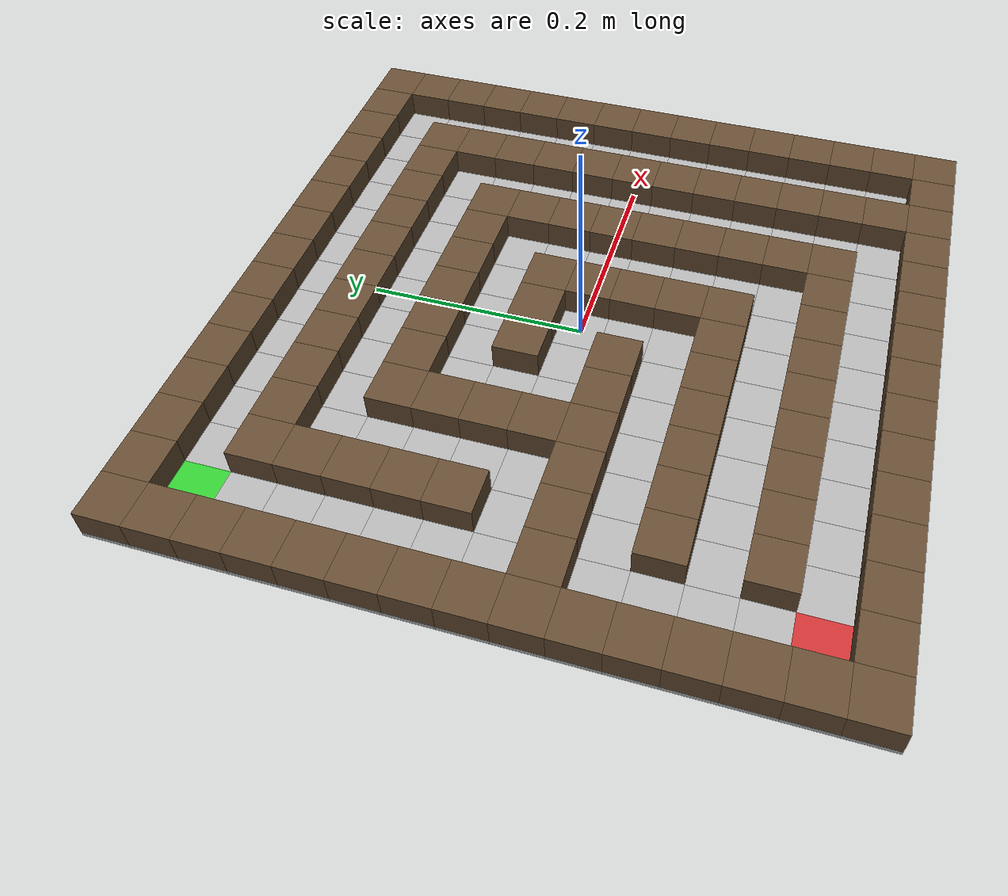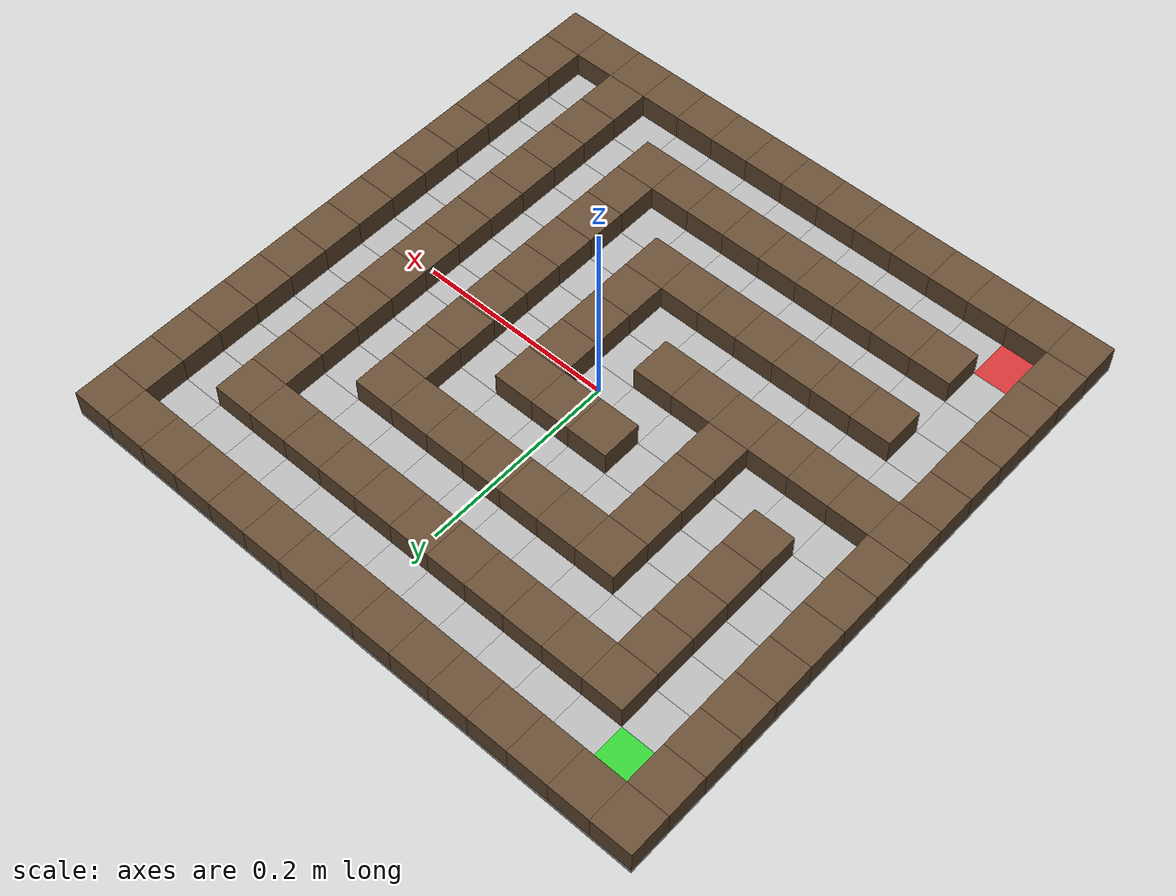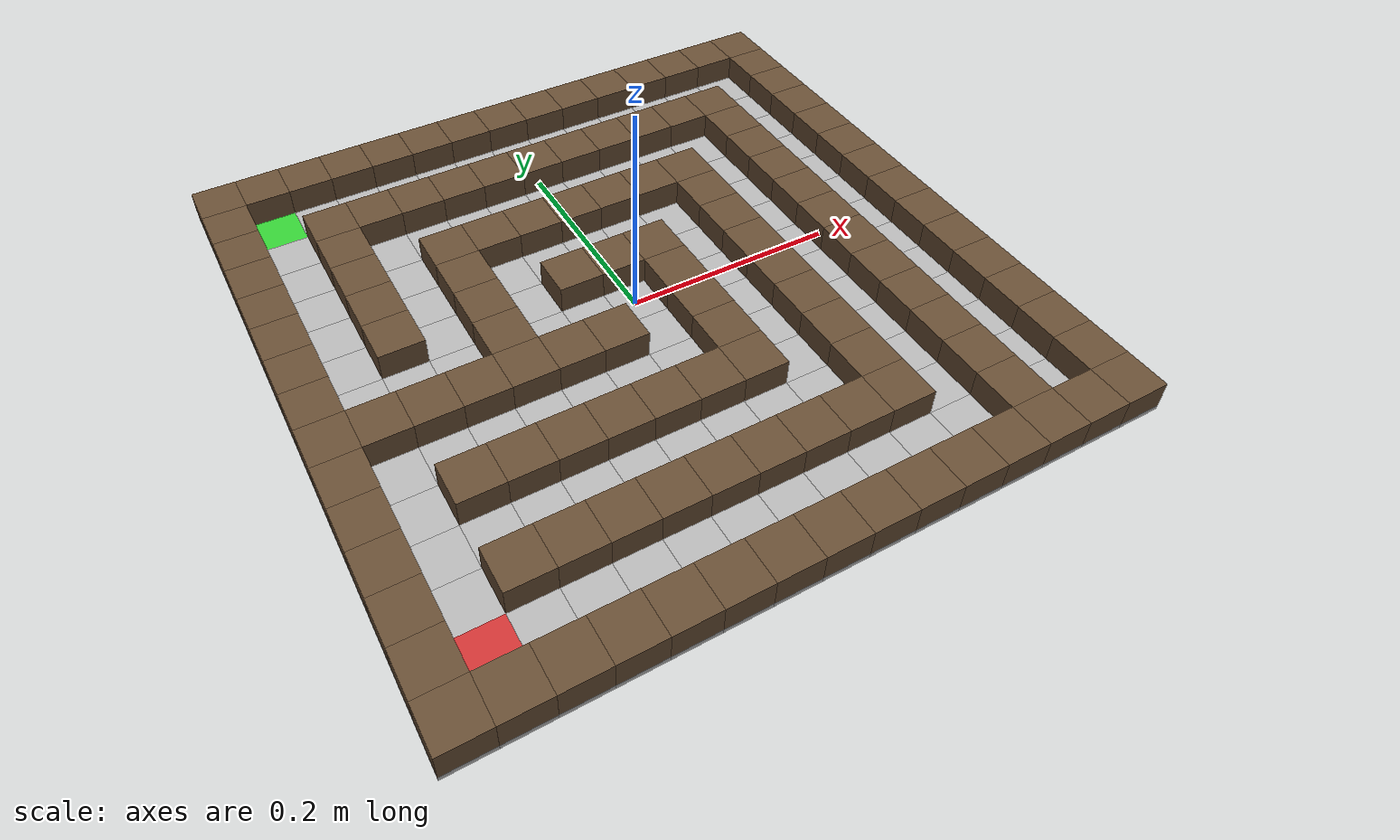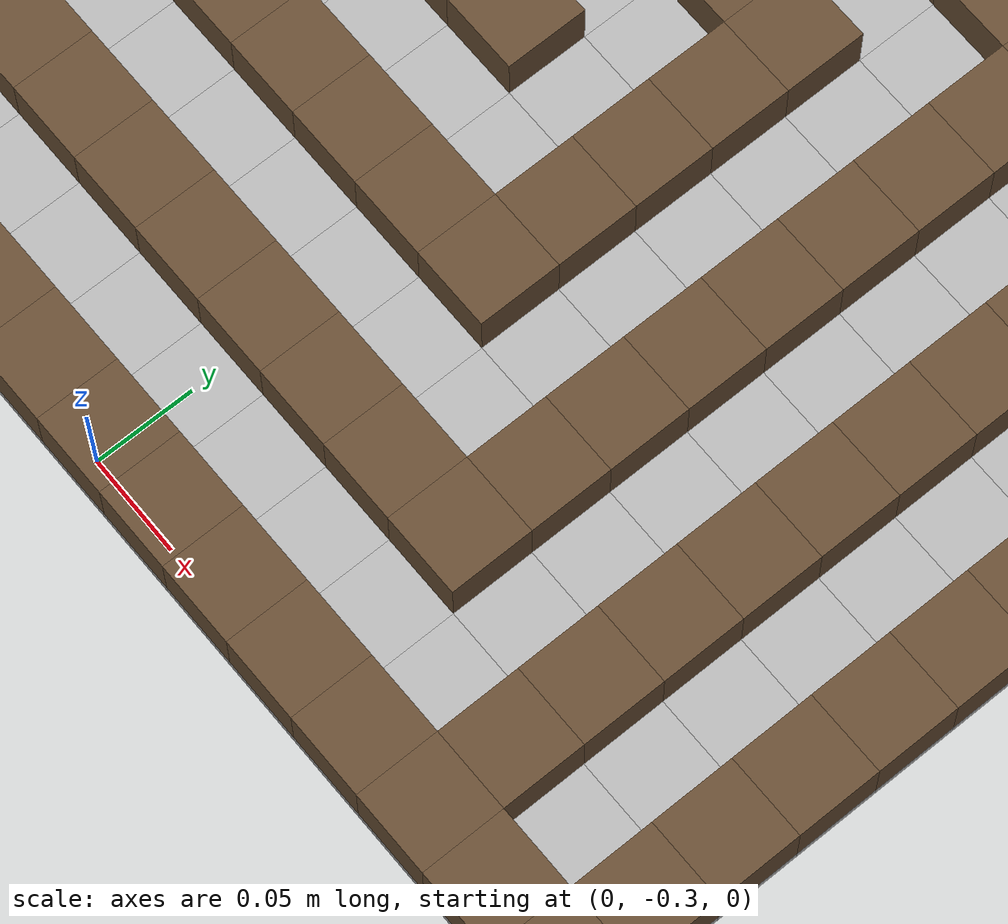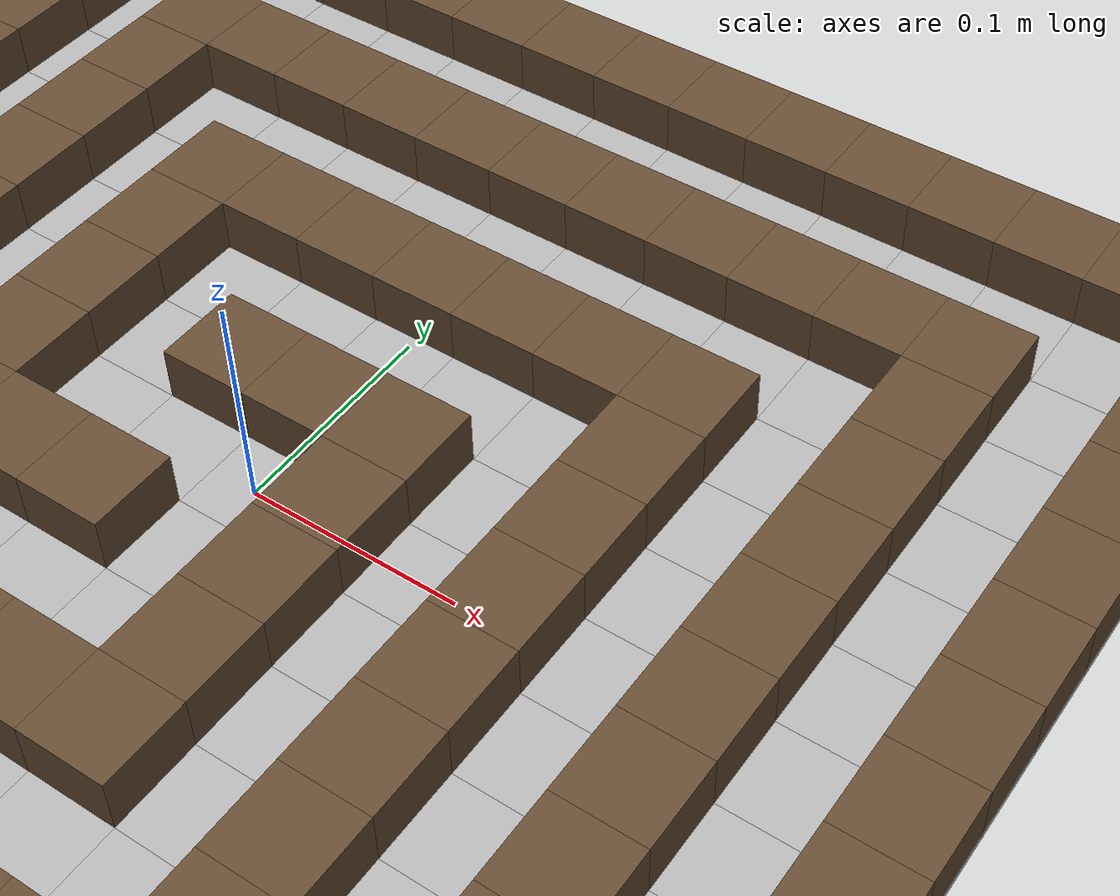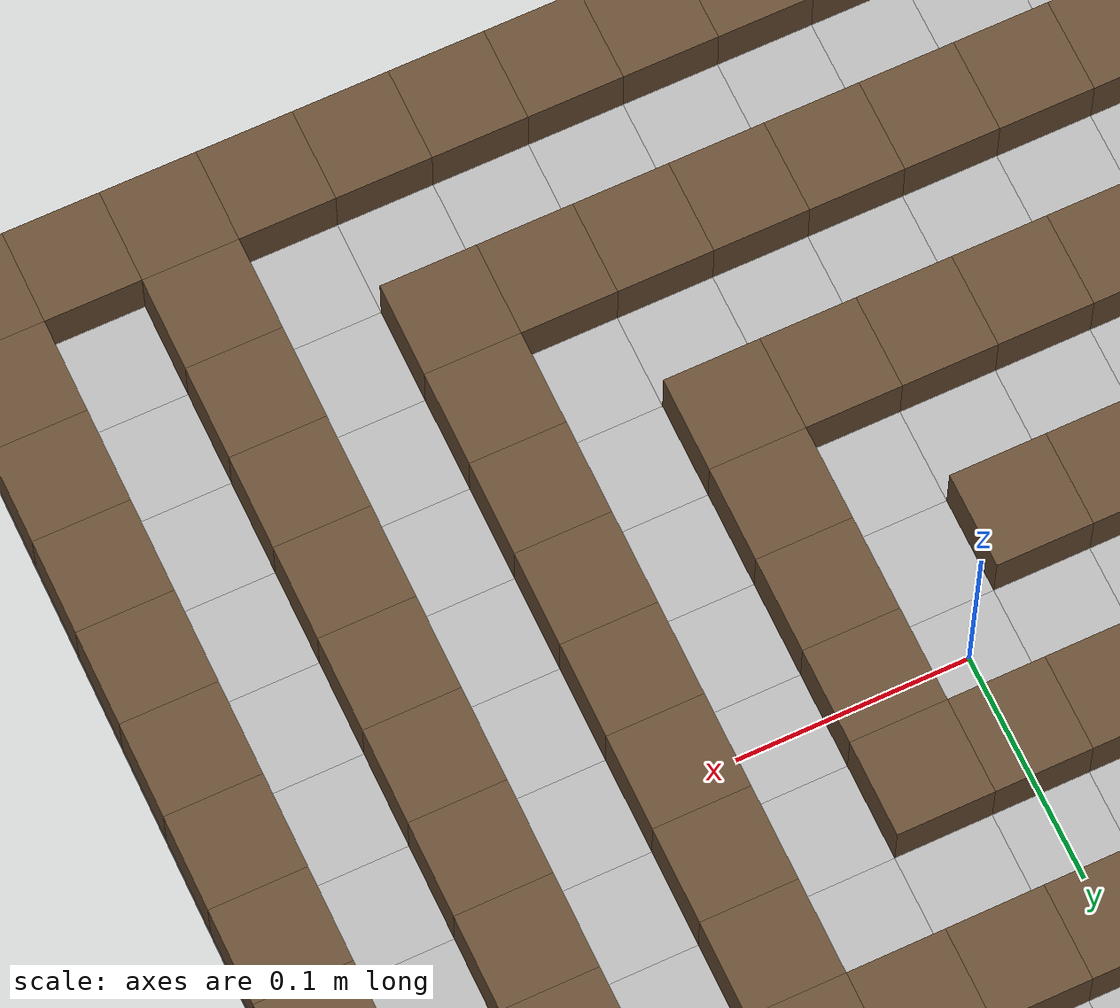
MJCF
<mujoco model="maze_structure">
  <asset>
    <texture name="tex_wall" type="2d" builtin="flat" rgb1="0.4 0.3 0.2" width="512" height="512"/>
    <material name="mat_wall" texture="tex_wall" shininess="0.1" specular="0.1"/>
  </asset>
  <worldbody>
    <body>
      <body name="object">

        <geom name="floor_col_0_0" type="box" group="1"
              size="0.0208 0.0208 0.0020"
              pos="-0.2912 0.2912 0"
              rgba="0.7 0.7 0.7 1"
              condim="3" contype="1" conaffinity="1"
              friction="0.01 0.005 0.0001" solref="0.002 1"/>

        <geom name="floor_col_0_1" type="box" group="1"
              size="0.0208 0.0208 0.0020"
              pos="-0.2496 0.2912 0"
              rgba="0.7 0.7 0.7 1"
              condim="3" contype="1" conaffinity="1"
              friction="0.01 0.005 0.0001" solref="0.002 1"/>

        <geom name="floor_col_0_2" type="box" group="1"
              size="0.0208 0.0208 0.0020"
              pos="-0.2080 0.2912 0"
              rgba="0.7 0.7 0.7 1"
              condim="3" contype="1" conaffinity="1"
              friction="0.01 0.005 0.0001" solref="0.002 1"/>

        <geom name="floor_col_0_3" type="box" group="1"
              size="0.0208 0.0208 0.0020"
              pos="-0.1664 0.2912 0"
              rgba="0.7 0.7 0.7 1"
              condim="3" contype="1" conaffinity="1"
              friction="0.01 0.005 0.0001" solref="0.002 1"/>

        <geom name="floor_col_0_4" type="box" group="1"
              size="0.0208 0.0208 0.0020"
              pos="-0.1248 0.2912 0"
              rgba="0.7 0.7 0.7 1"
              condim="3" contype="1" conaffinity="1"
              friction="0.01 0.005 0.0001" solref="0.002 1"/>

        <geom name="floor_col_0_5" type="box" group="1"
              size="0.0208 0.0208 0.0020"
              pos="-0.0832 0.2912 0"
              rgba="0.7 0.7 0.7 1"
              condim="3" contype="1" conaffinity="1"
              friction="0.01 0.005 0.0001" solref="0.002 1"/>

        <geom name="floor_col_0_6" type="box" group="1"
              size="0.0208 0.0208 0.0020"
              pos="-0.0416 0.2912 0"
              rgba="0.7 0.7 0.7 1"
              condim="3" contype="1" conaffinity="1"
              friction="0.01 0.005 0.0001" solref="0.002 1"/>

        <geom name="floor_col_0_7" type="box" group="1"
              size="0.0208 0.0208 0.0020"
              pos="0.0000 0.2912 0"
              rgba="0.7 0.7 0.7 1"
              condim="3" contype="1" conaffinity="1"
              friction="0.01 0.005 0.0001" solref="0.002 1"/>

        <geom name="floor_col_0_8" type="box" group="1"
              size="0.0208 0.0208 0.0020"
              pos="0.0416 0.2912 0"
              rgba="0.7 0.7 0.7 1"
              condim="3" contype="1" conaffinity="1"
              friction="0.01 0.005 0.0001" solref="0.002 1"/>

        <geom name="floor_col_0_9" type="box" group="1"
              size="0.0208 0.0208 0.0020"
              pos="0.0832 0.2912 0"
              rgba="0.7 0.7 0.7 1"
              condim="3" contype="1" conaffinity="1"
              friction="0.01 0.005 0.0001" solref="0.002 1"/>

        <geom name="floor_col_0_10" type="box" group="1"
              size="0.0208 0.0208 0.0020"
              pos="0.1248 0.2912 0"
              rgba="0.7 0.7 0.7 1"
              condim="3" contype="1" conaffinity="1"
              friction="0.01 0.005 0.0001" solref="0.002 1"/>

        <geom name="floor_col_0_11" type="box" group="1"
              size="0.0208 0.0208 0.0020"
              pos="0.1664 0.2912 0"
              rgba="0.7 0.7 0.7 1"
              condim="3" contype="1" conaffinity="1"
              friction="0.01 0.005 0.0001" solref="0.002 1"/>

        <geom name="floor_col_0_12" type="box" group="1"
              size="0.0208 0.0208 0.0020"
              pos="0.2080 0.2912 0"
              rgba="0.7 0.7 0.7 1"
              condim="3" contype="1" conaffinity="1"
              friction="0.01 0.005 0.0001" solref="0.002 1"/>

        <geom name="floor_col_0_13" type="box" group="1"
              size="0.0208 0.0208 0.0020"
              pos="0.2496 0.2912 0"
              rgba="0.7 0.7 0.7 1"
              condim="3" contype="1" conaffinity="1"
              friction="0.01 0.005 0.0001" solref="0.002 1"/>

        <geom name="floor_col_0_14" type="box" group="1"
              size="0.0208 0.0208 0.0020"
              pos="0.2912 0.2912 0"
              rgba="0.7 0.7 0.7 1"
              condim="3" contype="1" conaffinity="1"
              friction="0.01 0.005 0.0001" solref="0.002 1"/>

        <geom name="floor_col_1_0" type="box" group="1"
              size="0.0208 0.0208 0.0020"
              pos="-0.2912 0.2496 0"
              rgba="0.7 0.7 0.7 1"
              condim="3" contype="1" conaffinity="1"
              friction="0.01 0.005 0.0001" solref="0.002 1"/>

        <geom name="floor_col_1_1" type="box" group="1"
              size="0.0208 0.0208 0.0020"
              pos="-0.2496 0.2496 0"
              rgba="0.2 0.8 0.2 1"
              condim="3" contype="1" conaffinity="1"
              friction="0.01 0.005 0.0001" solref="0.002 1"/>

        <geom name="floor_col_1_2" type="box" group="1"
              size="0.0208 0.0208 0.0020"
              pos="-0.2080 0.2496 0"
              rgba="0.7 0.7 0.7 1"
              condim="3" contype="1" conaffinity="1"
              friction="0.01 0.005 0.0001" solref="0.002 1"/>

        <geom name="floor_col_1_3" type="box" group="1"
              size="0.0208 0.0208 0.0020"
              pos="-0.1664 0.2496 0"
              rgba="0.7 0.7 0.7 1"
              condim="3" contype="1" conaffinity="1"
              friction="0.01 0.005 0.0001" solref="0.002 1"/>

        <geom name="floor_col_1_4" type="box" group="1"
              size="0.0208 0.0208 0.0020"
              pos="-0.1248 0.2496 0"
              rgba="0.7 0.7 0.7 1"
              condim="3" contype="1" conaffinity="1"
              friction="0.01 0.005 0.0001" solref="0.002 1"/>

        <geom name="floor_col_1_5" type="box" group="1"
              size="0.0208 0.0208 0.0020"
              pos="-0.0832 0.2496 0"
              rgba="0.7 0.7 0.7 1"
              condim="3" contype="1" conaffinity="1"
              friction="0.01 0.005 0.0001" solref="0.002 1"/>

        <geom name="floor_col_1_6" type="box" group="1"
              size="0.0208 0.0208 0.0020"
              pos="-0.0416 0.2496 0"
              rgba="0.7 0.7 0.7 1"
              condim="3" contype="1" conaffinity="1"
              friction="0.01 0.005 0.0001" solref="0.002 1"/>

        <geom name="floor_col_1_7" type="box" group="1"
              size="0.0208 0.0208 0.0020"
              pos="0.0000 0.2496 0"
              rgba="0.7 0.7 0.7 1"
              condim="3" contype="1" conaffinity="1"
              friction="0.01 0.005 0.0001" solref="0.002 1"/>

        <geom name="floor_col_1_8" type="box" group="1"
              size="0.0208 0.0208 0.0020"
              pos="0.0416 0.2496 0"
              rgba="0.7 0.7 0.7 1"
              condim="3" contype="1" conaffinity="1"
              friction="0.01 0.005 0.0001" solref="0.002 1"/>

        <geom name="floor_col_1_9" type="box" group="1"
              size="0.0208 0.0208 0.0020"
              pos="0.0832 0.2496 0"
              rgba="0.7 0.7 0.7 1"
              condim="3" contype="1" conaffinity="1"
              friction="0.01 0.005 0.0001" solref="0.002 1"/>

        <geom name="floor_col_1_10" type="box" group="1"
              size="0.0208 0.0208 0.0020"
              pos="0.1248 0.2496 0"
              rgba="0.7 0.7 0.7 1"
              condim="3" contype="1" conaffinity="1"
              friction="0.01 0.005 0.0001" solref="0.002 1"/>

        <geom name="floor_col_1_11" type="box" group="1"
              size="0.0208 0.0208 0.0020"
              pos="0.1664 0.2496 0"
              rgba="0.7 0.7 0.7 1"
              condim="3" contype="1" conaffinity="1"
              friction="0.01 0.005 0.0001" solref="0.002 1"/>

        <geom name="floor_col_1_12" type="box" group="1"
              size="0.0208 0.0208 0.0020"
              pos="0.2080 0.2496 0"
              rgba="0.7 0.7 0.7 1"
              condim="3" contype="1" conaffinity="1"
              friction="0.01 0.005 0.0001" solref="0.002 1"/>

        <geom name="floor_col_1_13" type="box" group="1"
              size="0.0208 0.0208 0.0020"
              pos="0.2496 0.2496 0"
              rgba="0.7 0.7 0.7 1"
              condim="3" contype="1" conaffinity="1"
              friction="0.01 0.005 0.0001" solref="0.002 1"/>

        <geom name="floor_col_1_14" type="box" group="1"
              size="0.0208 0.0208 0.0020"
              pos="0.2912 0.2496 0"
              rgba="0.7 0.7 0.7 1"
              condim="3" contype="1" conaffinity="1"
              friction="0.01 0.005 0.0001" solref="0.002 1"/>

        <geom name="floor_col_2_0" type="box" group="1"
              size="0.0208 0.0208 0.0020"
              pos="-0.2912 0.2080 0"
              rgba="0.7 0.7 0.7 1"
              condim="3" contype="1" conaffinity="1"
              friction="0.01 0.005 0.0001" solref="0.002 1"/>

        <geom name="floor_col_2_1" type="box" group="1"
              size="0.0208 0.0208 0.0020"
              pos="-0.2496 0.2080 0"
              rgba="0.7 0.7 0.7 1"
              condim="3" contype="1" conaffinity="1"
              friction="0.01 0.005 0.0001" solref="0.002 1"/>

        <geom name="floor_col_2_2" type="box" group="1"
              size="0.0208 0.0208 0.0020"
              pos="-0.2080 0.2080 0"
              rgba="0.7 0.7 0.7 1"
              condim="3" contype="1" conaffinity="1"
              friction="0.01 0.005 0.0001" solref="0.002 1"/>

        <geom name="floor_col_2_3" type="box" group="1"
              size="0.0208 0.0208 0.0020"
              pos="-0.1664 0.2080 0"
              rgba="0.7 0.7 0.7 1"
              condim="3" contype="1" conaffinity="1"
              friction="0.01 0.005 0.0001" solref="0.002 1"/>

        <geom name="floor_col_2_4" type="box" group="1"
              size="0.0208 0.0208 0.0020"
              pos="-0.1248 0.2080 0"
              rgba="0.7 0.7 0.7 1"
              condim="3" contype="1" conaffinity="1"
              friction="0.01 0.005 0.0001" solref="0.002 1"/>

        <geom name="floor_col_2_5" type="box" group="1"
              size="0.0208 0.0208 0.0020"
              pos="-0.0832 0.2080 0"
              rgba="0.7 0.7 0.7 1"
              condim="3" contype="1" conaffinity="1"
              friction="0.01 0.005 0.0001" solref="0.002 1"/>

        <geom name="floor_col_2_6" type="box" group="1"
              size="0.0208 0.0208 0.0020"
              pos="-0.0416 0.2080 0"
              rgba="0.7 0.7 0.7 1"
              condim="3" contype="1" conaffinity="1"
              friction="0.01 0.005 0.0001" solref="0.002 1"/>

        <geom name="floor_col_2_7" type="box" group="1"
              size="0.0208 0.0208 0.0020"
              pos="0.0000 0.2080 0"
              rgba="0.7 0.7 0.7 1"
              condim="3" contype="1" conaffinity="1"
              friction="0.01 0.005 0.0001" solref="0.002 1"/>

        <geom name="floor_col_2_8" type="box" group="1"
              size="0.0208 0.0208 0.0020"
              pos="0.0416 0.2080 0"
              rgba="0.7 0.7 0.7 1"
              condim="3" contype="1" conaffinity="1"
              friction="0.01 0.005 0.0001" solref="0.002 1"/>

        <geom name="floor_col_2_9" type="box" group="1"
              size="0.0208 0.0208 0.0020"
              pos="0.0832 0.2080 0"
              rgba="0.7 0.7 0.7 1"
              condim="3" contype="1" conaffinity="1"
              friction="0.01 0.005 0.0001" solref="0.002 1"/>

        <geom name="floor_col_2_10" type="box" group="1"
              size="0.0208 0.0208 0.0020"
              pos="0.1248 0.2080 0"
              rgba="0.7 0.7 0.7 1"
              condim="3" contype="1" conaffinity="1"
              friction="0.01 0.005 0.0001" solref="0.002 1"/>

        <geom name="floor_col_2_11" type="box" group="1"
              size="0.0208 0.0208 0.0020"
              pos="0.1664 0.2080 0"
              rgba="0.7 0.7 0.7 1"
              condim="3" contype="1" conaffinity="1"
              friction="0.01 0.005 0.0001" solref="0.002 1"/>

        <geom name="floor_col_2_12" type="box" group="1"
              size="0.0208 0.0208 0.0020"
              pos="0.2080 0.2080 0"
              rgba="0.7 0.7 0.7 1"
              condim="3" contype="1" conaffinity="1"
              friction="0.01 0.005 0.0001" solref="0.002 1"/>

        <geom name="floor_col_2_13" type="box" group="1"
              size="0.0208 0.0208 0.0020"
              pos="0.2496 0.2080 0"
              rgba="0.7 0.7 0.7 1"
              condim="3" contype="1" conaffinity="1"
              friction="0.01 0.005 0.0001" solref="0.002 1"/>

        <geom name="floor_col_2_14" type="box" group="1"
              size="0.0208 0.0208 0.0020"
              pos="0.2912 0.2080 0"
              rgba="0.7 0.7 0.7 1"
              condim="3" contype="1" conaffinity="1"
              friction="0.01 0.005 0.0001" solref="0.002 1"/>

        <geom name="floor_col_3_0" type="box" group="1"
              size="0.0208 0.0208 0.0020"
              pos="-0.2912 0.1664 0"
              rgba="0.7 0.7 0.7 1"
              condim="3" contype="1" conaffinity="1"
              friction="0.01 0.005 0.0001" solref="0.002 1"/>

        <geom name="floor_col_3_1" type="box" group="1"
              size="0.0208 0.0208 0.0020"
              pos="-0.2496 0.1664 0"
              rgba="0.7 0.7 0.7 1"
              condim="3" contype="1" conaffinity="1"
              friction="0.01 0.005 0.0001" solref="0.002 1"/>

        <geom name="floor_col_3_2" type="box" group="1"
              size="0.0208 0.0208 0.0020"
              pos="-0.2080 0.1664 0"
              rgba="0.7 0.7 0.7 1"
              condim="3" contype="1" conaffinity="1"
              friction="0.01 0.005 0.0001" solref="0.002 1"/>

        <geom name="floor_col_3_3" type="box" group="1"
              size="0.0208 0.0208 0.0020"
              pos="-0.1664 0.1664 0"
              rgba="0.7 0.7 0.7 1"
              condim="3" contype="1" conaffinity="1"
              friction="0.01 0.005 0.0001" solref="0.002 1"/>

        <geom name="floor_col_3_4" type="box" group="1"
              size="0.0208 0.0208 0.0020"
              pos="-0.1248 0.1664 0"
              rgba="0.7 0.7 0.7 1"
              condim="3" contype="1" conaffinity="1"
              friction="0.01 0.005 0.0001" solref="0.002 1"/>

        <geom name="floor_col_3_5" type="box" group="1"
              size="0.0208 0.0208 0.0020"
              pos="-0.0832 0.1664 0"
              rgba="0.7 0.7 0.7 1"
              condim="3" contype="1" conaffinity="1"
              friction="0.01 0.005 0.0001" solref="0.002 1"/>

        <geom name="floor_col_3_6" type="box" group="1"
              size="0.0208 0.0208 0.0020"
              pos="-0.0416 0.1664 0"
              rgba="0.7 0.7 0.7 1"
              condim="3" contype="1" conaffinity="1"
              friction="0.01 0.005 0.0001" solref="0.002 1"/>

        <geom name="floor_col_3_7" type="box" group="1"
              size="0.0208 0.0208 0.0020"
              pos="0.0000 0.1664 0"
              rgba="0.7 0.7 0.7 1"
              condim="3" contype="1" conaffinity="1"
              friction="0.01 0.005 0.0001" solref="0.002 1"/>

        <geom name="floor_col_3_8" type="box" group="1"
              size="0.0208 0.0208 0.0020"
              pos="0.0416 0.1664 0"
              rgba="0.7 0.7 0.7 1"
              condim="3" contype="1" conaffinity="1"
              friction="0.01 0.005 0.0001" solref="0.002 1"/>

        <geom name="floor_col_3_9" type="box" group="1"
              size="0.0208 0.0208 0.0020"
              pos="0.0832 0.1664 0"
              rgba="0.7 0.7 0.7 1"
              condim="3" contype="1" conaffinity="1"
              friction="0.01 0.005 0.0001" solref="0.002 1"/>

        <geom name="floor_col_3_10" type="box" group="1"
              size="0.0208 0.0208 0.0020"
              pos="0.1248 0.1664 0"
              rgba="0.7 0.7 0.7 1"
              condim="3" contype="1" conaffinity="1"
              friction="0.01 0.005 0.0001" solref="0.002 1"/>

        <geom name="floor_col_3_11" type="box" group="1"
              size="0.0208 0.0208 0.0020"
              pos="0.1664 0.1664 0"
              rgba="0.7 0.7 0.7 1"
              condim="3" contype="1" conaffinity="1"
              friction="0.01 0.005 0.0001" solref="0.002 1"/>

        <geom name="floor_col_3_12" type="box" group="1"
              size="0.0208 0.0208 0.0020"
              pos="0.2080 0.1664 0"
              rgba="0.7 0.7 0.7 1"
              condim="3" contype="1" conaffinity="1"
              friction="0.01 0.005 0.0001" solref="0.002 1"/>

        <geom name="floor_col_3_13" type="box" group="1"
              size="0.0208 0.0208 0.0020"
              pos="0.2496 0.1664 0"
              rgba="0.7 0.7 0.7 1"
              condim="3" contype="1" conaffinity="1"
              friction="0.01 0.005 0.0001" solref="0.002 1"/>

        <geom name="floor_col_3_14" type="box" group="1"
              size="0.0208 0.0208 0.0020"
              pos="0.2912 0.1664 0"
              rgba="0.7 0.7 0.7 1"
              condim="3" contype="1" conaffinity="1"
              friction="0.01 0.005 0.0001" solref="0.002 1"/>

        <geom name="floor_col_4_0" type="box" group="1"
              size="0.0208 0.0208 0.0020"
              pos="-0.2912 0.1248 0"
              rgba="0.7 0.7 0.7 1"
              condim="3" contype="1" conaffinity="1"
              friction="0.01 0.005 0.0001" solref="0.002 1"/>

        <geom name="floor_col_4_1" type="box" group="1"
              size="0.0208 0.0208 0.0020"
              pos="-0.2496 0.1248 0"
              rgba="0.7 0.7 0.7 1"
              condim="3" contype="1" conaffinity="1"
              friction="0.01 0.005 0.0001" solref="0.002 1"/>

        <geom name="floor_col_4_2" type="box" group="1"
              size="0.0208 0.0208 0.0020"
              pos="-0.2080 0.1248 0"
              rgba="0.7 0.7 0.7 1"
              condim="3" contype="1" conaffinity="1"
              friction="0.01 0.005 0.0001" solref="0.002 1"/>

        <geom name="floor_col_4_3" type="box" group="1"
              size="0.0208 0.0208 0.0020"
              pos="-0.1664 0.1248 0"
              rgba="0.7 0.7 0.7 1"
              condim="3" contype="1" conaffinity="1"
              friction="0.01 0.005 0.0001" solref="0.002 1"/>

        <geom name="floor_col_4_4" type="box" group="1"
              size="0.0208 0.0208 0.0020"
              pos="-0.1248 0.1248 0"
              rgba="0.7 0.7 0.7 1"
              condim="3" contype="1" conaffinity="1"
              friction="0.01 0.005 0.0001" solref="0.002 1"/>

        <geom name="floor_col_4_5" type="box" group="1"
              size="0.0208 0.0208 0.0020"
              pos="-0.0832 0.1248 0"
              rgba="0.7 0.7 0.7 1"
              condim="3" contype="1" conaffinity="1"
              friction="0.01 0.005 0.0001" solref="0.002 1"/>

        <geom name="floor_col_4_6" type="box" group="1"
              size="0.0208 0.0208 0.0020"
              pos="-0.0416 0.1248 0"
              rgba="0.7 0.7 0.7 1"
              condim="3" contype="1" conaffinity="1"
              friction="0.01 0.005 0.0001" solref="0.002 1"/>

        <geom name="floor_col_4_7" type="box" group="1"
              size="0.0208 0.0208 0.0020"
              pos="0.0000 0.1248 0"
              rgba="0.7 0.7 0.7 1"
              condim="3" contype="1" conaffinity="1"
              friction="0.01 0.005 0.0001" solref="0.002 1"/>

        <geom name="floor_col_4_8" type="box" group="1"
              size="0.0208 0.0208 0.0020"
              pos="0.0416 0.1248 0"
              rgba="0.7 0.7 0.7 1"
              condim="3" contype="1" conaffinity="1"
              friction="0.01 0.005 0.0001" solref="0.002 1"/>

        <geom name="floor_col_4_9" type="box" group="1"
              size="0.0208 0.0208 0.0020"
              pos="0.0832 0.1248 0"
              rgba="0.7 0.7 0.7 1"
              condim="3" contype="1" conaffinity="1"
              friction="0.01 0.005 0.0001" solref="0.002 1"/>

        <geom name="floor_col_4_10" type="box" group="1"
              size="0.0208 0.0208 0.0020"
              pos="0.1248 0.1248 0"
              rgba="0.7 0.7 0.7 1"
              condim="3" contype="1" conaffinity="1"
              friction="0.01 0.005 0.0001" solref="0.002 1"/>

        <geom name="floor_col_4_11" type="box" group="1"
              size="0.0208 0.0208 0.0020"
              pos="0.1664 0.1248 0"
              rgba="0.7 0.7 0.7 1"
              condim="3" contype="1" conaffinity="1"
              friction="0.01 0.005 0.0001" solref="0.002 1"/>

        <geom name="floor_col_4_12" type="box" group="1"
              size="0.0208 0.0208 0.0020"
              pos="0.2080 0.1248 0"
              rgba="0.7 0.7 0.7 1"
              condim="3" contype="1" conaffinity="1"
              friction="0.01 0.005 0.0001" solref="0.002 1"/>

        <geom name="floor_col_4_13" type="box" group="1"
              size="0.0208 0.0208 0.0020"
              pos="0.2496 0.1248 0"
              rgba="0.7 0.7 0.7 1"
              condim="3" contype="1" conaffinity="1"
              friction="0.01 0.005 0.0001" solref="0.002 1"/>

        <geom name="floor_col_4_14" type="box" group="1"
              size="0.0208 0.0208 0.0020"
              pos="0.2912 0.1248 0"
              rgba="0.7 0.7 0.7 1"
              condim="3" contype="1" conaffinity="1"
              friction="0.01 0.005 0.0001" solref="0.002 1"/>

        <geom name="floor_col_5_0" type="box" group="1"
              size="0.0208 0.0208 0.0020"
              pos="-0.2912 0.0832 0"
              rgba="0.7 0.7 0.7 1"
              condim="3" contype="1" conaffinity="1"
              friction="0.01 0.005 0.0001" solref="0.002 1"/>

        <geom name="floor_col_5_1" type="box" group="1"
              size="0.0208 0.0208 0.0020"
              pos="-0.2496 0.0832 0"
              rgba="0.7 0.7 0.7 1"
              condim="3" contype="1" conaffinity="1"
              friction="0.01 0.005 0.0001" solref="0.002 1"/>

        <geom name="floor_col_5_2" type="box" group="1"
              size="0.0208 0.0208 0.0020"
              pos="-0.2080 0.0832 0"
              rgba="0.7 0.7 0.7 1"
              condim="3" contype="1" conaffinity="1"
              friction="0.01 0.005 0.0001" solref="0.002 1"/>

        <geom name="floor_col_5_3" type="box" group="1"
              size="0.0208 0.0208 0.0020"
              pos="-0.1664 0.0832 0"
              rgba="0.7 0.7 0.7 1"
              condim="3" contype="1" conaffinity="1"
              friction="0.01 0.005 0.0001" solref="0.002 1"/>

        <geom name="floor_col_5_4" type="box" group="1"
              size="0.0208 0.0208 0.0020"
              pos="-0.1248 0.0832 0"
              rgba="0.7 0.7 0.7 1"
              condim="3" contype="1" conaffinity="1"
              friction="0.01 0.005 0.0001" solref="0.002 1"/>

        <geom name="floor_col_5_5" type="box" group="1"
              size="0.0208 0.0208 0.0020"
              pos="-0.0832 0.0832 0"
              rgba="0.7 0.7 0.7 1"
              condim="3" contype="1" conaffinity="1"
              friction="0.01 0.005 0.0001" solref="0.002 1"/>

        <geom name="floor_col_5_6" type="box" group="1"
              size="0.0208 0.0208 0.0020"
              pos="-0.0416 0.0832 0"
              rgba="0.7 0.7 0.7 1"
              condim="3" contype="1" conaffinity="1"
              friction="0.01 0.005 0.0001" solref="0.002 1"/>

        <geom name="floor_col_5_7" type="box" group="1"
              size="0.0208 0.0208 0.0020"
              pos="0.0000 0.0832 0"
              rgba="0.7 0.7 0.7 1"
              condim="3" contype="1" conaffinity="1"
              friction="0.01 0.005 0.0001" solref="0.002 1"/>

        <geom name="floor_col_5_8" type="box" group="1"
              size="0.0208 0.0208 0.0020"
              pos="0.0416 0.0832 0"
              rgba="0.7 0.7 0.7 1"
              condim="3" contype="1" conaffinity="1"
              friction="0.01 0.005 0.0001" solref="0.002 1"/>

        <geom name="floor_col_5_9" type="box" group="1"
              size="0.0208 0.0208 0.0020"
              pos="0.0832 0.0832 0"
              rgba="0.7 0.7 0.7 1"
              condim="3" contype="1" conaffinity="1"
              friction="0.01 0.005 0.0001" solref="0.002 1"/>

        <geom name="floor_col_5_10" type="box" group="1"
              size="0.0208 0.0208 0.0020"
              pos="0.1248 0.0832 0"
              rgba="0.7 0.7 0.7 1"
              condim="3" contype="1" conaffinity="1"
              friction="0.01 0.005 0.0001" solref="0.002 1"/>

        <geom name="floor_col_5_11" type="box" group="1"
              size="0.0208 0.0208 0.0020"
              pos="0.1664 0.0832 0"
              rgba="0.7 0.7 0.7 1"
              condim="3" contype="1" conaffinity="1"
              friction="0.01 0.005 0.0001" solref="0.002 1"/>

        <geom name="floor_col_5_12" type="box" group="1"
              size="0.0208 0.0208 0.0020"
              pos="0.2080 0.0832 0"
              rgba="0.7 0.7 0.7 1"
              condim="3" contype="1" conaffinity="1"
              friction="0.01 0.005 0.0001" solref="0.002 1"/>

        <geom name="floor_col_5_13" type="box" group="1"
              size="0.0208 0.0208 0.0020"
              pos="0.2496 0.0832 0"
              rgba="0.7 0.7 0.7 1"
              condim="3" contype="1" conaffinity="1"
              friction="0.01 0.005 0.0001" solref="0.002 1"/>

        <geom name="floor_col_5_14" type="box" group="1"
              size="0.0208 0.0208 0.0020"
              pos="0.2912 0.0832 0"
              rgba="0.7 0.7 0.7 1"
              condim="3" contype="1" conaffinity="1"
              friction="0.01 0.005 0.0001" solref="0.002 1"/>

        <geom name="floor_col_6_0" type="box" group="1"
              size="0.0208 0.0208 0.0020"
              pos="-0.2912 0.0416 0"
              rgba="0.7 0.7 0.7 1"
              condim="3" contype="1" conaffinity="1"
              friction="0.01 0.005 0.0001" solref="0.002 1"/>

        <geom name="floor_col_6_1" type="box" group="1"
              size="0.0208 0.0208 0.0020"
              pos="-0.2496 0.0416 0"
              rgba="0.7 0.7 0.7 1"
              condim="3" contype="1" conaffinity="1"
              friction="0.01 0.005 0.0001" solref="0.002 1"/>

        <geom name="floor_col_6_2" type="box" group="1"
              size="0.0208 0.0208 0.0020"
              pos="-0.2080 0.0416 0"
              rgba="0.7 0.7 0.7 1"
              condim="3" contype="1" conaffinity="1"
              friction="0.01 0.005 0.0001" solref="0.002 1"/>

        <geom name="floor_col_6_3" type="box" group="1"
              size="0.0208 0.0208 0.0020"
              pos="-0.1664 0.0416 0"
              rgba="0.7 0.7 0.7 1"
              condim="3" contype="1" conaffinity="1"
              friction="0.01 0.005 0.0001" solref="0.002 1"/>

        <geom name="floor_col_6_4" type="box" group="1"
              size="0.0208 0.0208 0.0020"
              pos="-0.1248 0.0416 0"
              rgba="0.7 0.7 0.7 1"
              condim="3" contype="1" conaffinity="1"
              friction="0.01 0.005 0.0001" solref="0.002 1"/>

        <geom name="floor_col_6_5" type="box" group="1"
              size="0.0208 0.0208 0.0020"
              pos="-0.0832 0.0416 0"
              rgba="0.7 0.7 0.7 1"
              condim="3" contype="1" conaffinity="1"
              friction="0.01 0.005 0.0001" solref="0.002 1"/>

        <geom name="floor_col_6_6" type="box" group="1"
              size="0.0208 0.0208 0.0020"
              pos="-0.0416 0.0416 0"
              rgba="0.7 0.7 0.7 1"
              condim="3" contype="1" conaffinity="1"
              friction="0.01 0.005 0.0001" solref="0.002 1"/>

        <geom name="floor_col_6_7" type="box" group="1"
              size="0.0208 0.0208 0.0020"
              pos="0.0000 0.0416 0"
              rgba="0.7 0.7 0.7 1"
              condim="3" contype="1" conaffinity="1"
              friction="0.01 0.005 0.0001" solref="0.002 1"/>

        <geom name="floor_col_6_8" type="box" group="1"
              size="0.0208 0.0208 0.0020"
              pos="0.0416 0.0416 0"
              rgba="0.7 0.7 0.7 1"
              condim="3" contype="1" conaffinity="1"
              friction="0.01 0.005 0.0001" solref="0.002 1"/>

        <geom name="floor_col_6_9" type="box" group="1"
              size="0.0208 0.0208 0.0020"
              pos="0.0832 0.0416 0"
              rgba="0.7 0.7 0.7 1"
              condim="3" contype="1" conaffinity="1"
              friction="0.01 0.005 0.0001" solref="0.002 1"/>

        <geom name="floor_col_6_10" type="box" group="1"
              size="0.0208 0.0208 0.0020"
              pos="0.1248 0.0416 0"
              rgba="0.7 0.7 0.7 1"
              condim="3" contype="1" conaffinity="1"
              friction="0.01 0.005 0.0001" solref="0.002 1"/>

        <geom name="floor_col_6_11" type="box" group="1"
              size="0.0208 0.0208 0.0020"
              pos="0.1664 0.0416 0"
              rgba="0.7 0.7 0.7 1"
              condim="3" contype="1" conaffinity="1"
              friction="0.01 0.005 0.0001" solref="0.002 1"/>

        <geom name="floor_col_6_12" type="box" group="1"
              size="0.0208 0.0208 0.0020"
              pos="0.2080 0.0416 0"
              rgba="0.7 0.7 0.7 1"
              condim="3" contype="1" conaffinity="1"
              friction="0.01 0.005 0.0001" solref="0.002 1"/>

        <geom name="floor_col_6_13" type="box" group="1"
              size="0.0208 0.0208 0.0020"
              pos="0.2496 0.0416 0"
              rgba="0.7 0.7 0.7 1"
              condim="3" contype="1" conaffinity="1"
              friction="0.01 0.005 0.0001" solref="0.002 1"/>

        <geom name="floor_col_6_14" type="box" group="1"
              size="0.0208 0.0208 0.0020"
              pos="0.2912 0.0416 0"
              rgba="0.7 0.7 0.7 1"
              condim="3" contype="1" conaffinity="1"
              friction="0.01 0.005 0.0001" solref="0.002 1"/>

        <geom name="floor_col_7_0" type="box" group="1"
              size="0.0208 0.0208 0.0020"
              pos="-0.2912 0.0000 0"
              rgba="0.7 0.7 0.7 1"
              condim="3" contype="1" conaffinity="1"
              friction="0.01 0.005 0.0001" solref="0.002 1"/>

        <geom name="floor_col_7_1" type="box" group="1"
              size="0.0208 0.0208 0.0020"
              pos="-0.2496 0.0000 0"
              rgba="0.7 0.7 0.7 1"
              condim="3" contype="1" conaffinity="1"
              friction="0.01 0.005 0.0001" solref="0.002 1"/>

        <geom name="floor_col_7_2" type="box" group="1"
              size="0.0208 0.0208 0.0020"
              pos="-0.2080 0.0000 0"
              rgba="0.7 0.7 0.7 1"
              condim="3" contype="1" conaffinity="1"
              friction="0.01 0.005 0.0001" solref="0.002 1"/>

        <geom name="floor_col_7_3" type="box" group="1"
              size="0.0208 0.0208 0.0020"
              pos="-0.1664 0.0000 0"
              rgba="0.7 0.7 0.7 1"
              condim="3" contype="1" conaffinity="1"
              friction="0.01 0.005 0.0001" solref="0.002 1"/>

        <geom name="floor_col_7_4" type="box" group="1"
              size="0.0208 0.0208 0.0020"
              pos="-0.1248 0.0000 0"
              rgba="0.7 0.7 0.7 1"
              condim="3" contype="1" conaffinity="1"
              friction="0.01 0.005 0.0001" solref="0.002 1"/>

        <geom name="floor_col_7_5" type="box" group="1"
              size="0.0208 0.0208 0.0020"
              pos="-0.0832 0.0000 0"
              rgba="0.7 0.7 0.7 1"
              condim="3" contype="1" conaffinity="1"
              friction="0.01 0.005 0.0001" solref="0.002 1"/>

        <geom name="floor_col_7_6" type="box" group="1"
              size="0.0208 0.0208 0.0020"
              pos="-0.0416 0.0000 0"
              rgba="0.7 0.7 0.7 1"
              condim="3" contype="1" conaffinity="1"
              friction="0.01 0.005 0.0001" solref="0.002 1"/>

        <geom name="floor_col_7_7" type="box" group="1"
              size="0.0208 0.0208 0.0020"
              pos="0.0000 0.0000 0"
              rgba="0.7 0.7 0.7 1"
              condim="3" contype="1" conaffinity="1"
              friction="0.01 0.005 0.0001" solref="0.002 1"/>

        <geom name="floor_col_7_8" type="box" group="1"
              size="0.0208 0.0208 0.0020"
              pos="0.0416 0.0000 0"
              rgba="0.7 0.7 0.7 1"
              condim="3" contype="1" conaffinity="1"
              friction="0.01 0.005 0.0001" solref="0.002 1"/>

        <geom name="floor_col_7_9" type="box" group="1"
              size="0.0208 0.0208 0.0020"
              pos="0.0832 0.0000 0"
              rgba="0.7 0.7 0.7 1"
              condim="3" contype="1" conaffinity="1"
              friction="0.01 0.005 0.0001" solref="0.002 1"/>

        <geom name="floor_col_7_10" type="box" group="1"
              size="0.0208 0.0208 0.0020"
              pos="0.1248 0.0000 0"
              rgba="0.7 0.7 0.7 1"
              condim="3" contype="1" conaffinity="1"
              friction="0.01 0.005 0.0001" solref="0.002 1"/>

        <geom name="floor_col_7_11" type="box" group="1"
              size="0.0208 0.0208 0.0020"
              pos="0.1664 0.0000 0"
              rgba="0.7 0.7 0.7 1"
              condim="3" contype="1" conaffinity="1"
              friction="0.01 0.005 0.0001" solref="0.002 1"/>

        <geom name="floor_col_7_12" type="box" group="1"
              size="0.0208 0.0208 0.0020"
              pos="0.2080 0.0000 0"
              rgba="0.7 0.7 0.7 1"
              condim="3" contype="1" conaffinity="1"
              friction="0.01 0.005 0.0001" solref="0.002 1"/>

        <geom name="floor_col_7_13" type="box" group="1"
              size="0.0208 0.0208 0.0020"
              pos="0.2496 0.0000 0"
              rgba="0.7 0.7 0.7 1"
              condim="3" contype="1" conaffinity="1"
              friction="0.01 0.005 0.0001" solref="0.002 1"/>

        <geom name="floor_col_7_14" type="box" group="1"
              size="0.0208 0.0208 0.0020"
              pos="0.2912 0.0000 0"
              rgba="0.7 0.7 0.7 1"
              condim="3" contype="1" conaffinity="1"
              friction="0.01 0.005 0.0001" solref="0.002 1"/>

        <geom name="floor_col_8_0" type="box" group="1"
              size="0.0208 0.0208 0.0020"
              pos="-0.2912 -0.0416 0"
              rgba="0.7 0.7 0.7 1"
              condim="3" contype="1" conaffinity="1"
              friction="0.01 0.005 0.0001" solref="0.002 1"/>

        <geom name="floor_col_8_1" type="box" group="1"
              size="0.0208 0.0208 0.0020"
              pos="-0.2496 -0.0416 0"
              rgba="0.7 0.7 0.7 1"
              condim="3" contype="1" conaffinity="1"
              friction="0.01 0.005 0.0001" solref="0.002 1"/>

        <geom name="floor_col_8_2" type="box" group="1"
              size="0.0208 0.0208 0.0020"
              pos="-0.2080 -0.0416 0"
              rgba="0.7 0.7 0.7 1"
              condim="3" contype="1" conaffinity="1"
              friction="0.01 0.005 0.0001" solref="0.002 1"/>

        <geom name="floor_col_8_3" type="box" group="1"
              size="0.0208 0.0208 0.0020"
              pos="-0.1664 -0.0416 0"
              rgba="0.7 0.7 0.7 1"
              condim="3" contype="1" conaffinity="1"
              friction="0.01 0.005 0.0001" solref="0.002 1"/>

        <geom name="floor_col_8_4" type="box" group="1"
              size="0.0208 0.0208 0.0020"
              pos="-0.1248 -0.0416 0"
              rgba="0.7 0.7 0.7 1"
              condim="3" contype="1" conaffinity="1"
              friction="0.01 0.005 0.0001" solref="0.002 1"/>

        <geom name="floor_col_8_5" type="box" group="1"
              size="0.0208 0.0208 0.0020"
              pos="-0.0832 -0.0416 0"
              rgba="0.7 0.7 0.7 1"
              condim="3" contype="1" conaffinity="1"
              friction="0.01 0.005 0.0001" solref="0.002 1"/>

        <geom name="floor_col_8_6" type="box" group="1"
              size="0.0208 0.0208 0.0020"
              pos="-0.0416 -0.0416 0"
              rgba="0.7 0.7 0.7 1"
              condim="3" contype="1" conaffinity="1"
              friction="0.01 0.005 0.0001" solref="0.002 1"/>

        <geom name="floor_col_8_7" type="box" group="1"
              size="0.0208 0.0208 0.0020"
              pos="0.0000 -0.0416 0"
              rgba="0.7 0.7 0.7 1"
              condim="3" contype="1" conaffinity="1"
              friction="0.01 0.005 0.0001" solref="0.002 1"/>

        <geom name="floor_col_8_8" type="box" group="1"
              size="0.0208 0.0208 0.0020"
              pos="0.0416 -0.0416 0"
              rgba="0.7 0.7 0.7 1"
              condim="3" contype="1" conaffinity="1"
              friction="0.01 0.005 0.0001" solref="0.002 1"/>

        <geom name="floor_col_8_9" type="box" group="1"
              size="0.0208 0.0208 0.0020"
              pos="0.0832 -0.0416 0"
              rgba="0.7 0.7 0.7 1"
              condim="3" contype="1" conaffinity="1"
              friction="0.01 0.005 0.0001" solref="0.002 1"/>

        <geom name="floor_col_8_10" type="box" group="1"
              size="0.0208 0.0208 0.0020"
              pos="0.1248 -0.0416 0"
              rgba="0.7 0.7 0.7 1"
              condim="3" contype="1" conaffinity="1"
              friction="0.01 0.005 0.0001" solref="0.002 1"/>

        <geom name="floor_col_8_11" type="box" group="1"
              size="0.0208 0.0208 0.0020"
              pos="0.1664 -0.0416 0"
              rgba="0.7 0.7 0.7 1"
              condim="3" contype="1" conaffinity="1"
              friction="0.01 0.005 0.0001" solref="0.002 1"/>

        <geom name="floor_col_8_12" type="box" group="1"
              size="0.0208 0.0208 0.0020"
              pos="0.2080 -0.0416 0"
              rgba="0.7 0.7 0.7 1"
              condim="3" contype="1" conaffinity="1"
              friction="0.01 0.005 0.0001" solref="0.002 1"/>

        <geom name="floor_col_8_13" type="box" group="1"
              size="0.0208 0.0208 0.0020"
              pos="0.2496 -0.0416 0"
              rgba="0.7 0.7 0.7 1"
              condim="3" contype="1" conaffinity="1"
              friction="0.01 0.005 0.0001" solref="0.002 1"/>

        <geom name="floor_col_8_14" type="box" group="1"
              size="0.0208 0.0208 0.0020"
              pos="0.2912 -0.0416 0"
              rgba="0.7 0.7 0.7 1"
              condim="3" contype="1" conaffinity="1"
              friction="0.01 0.005 0.0001" solref="0.002 1"/>

        <geom name="floor_col_9_0" type="box" group="1"
              size="0.0208 0.0208 0.0020"
              pos="-0.2912 -0.0832 0"
              rgba="0.7 0.7 0.7 1"
              condim="3" contype="1" conaffinity="1"
              friction="0.01 0.005 0.0001" solref="0.002 1"/>

        <geom name="floor_col_9_1" type="box" group="1"
              size="0.0208 0.0208 0.0020"
              pos="-0.2496 -0.0832 0"
              rgba="0.7 0.7 0.7 1"
              condim="3" contype="1" conaffinity="1"
              friction="0.01 0.005 0.0001" solref="0.002 1"/>

        <geom name="floor_col_9_2" type="box" group="1"
              size="0.0208 0.0208 0.0020"
              pos="-0.2080 -0.0832 0"
              rgba="0.7 0.7 0.7 1"
              condim="3" contype="1" conaffinity="1"
              friction="0.01 0.005 0.0001" solref="0.002 1"/>

        <geom name="floor_col_9_3" type="box" group="1"
              size="0.0208 0.0208 0.0020"
              pos="-0.1664 -0.0832 0"
              rgba="0.7 0.7 0.7 1"
              condim="3" contype="1" conaffinity="1"
              friction="0.01 0.005 0.0001" solref="0.002 1"/>

        <geom name="floor_col_9_4" type="box" group="1"
              size="0.0208 0.0208 0.0020"
              pos="-0.1248 -0.0832 0"
              rgba="0.7 0.7 0.7 1"
              condim="3" contype="1" conaffinity="1"
              friction="0.01 0.005 0.0001" solref="0.002 1"/>

        <geom name="floor_col_9_5" type="box" group="1"
              size="0.0208 0.0208 0.0020"
              pos="-0.0832 -0.0832 0"
              rgba="0.7 0.7 0.7 1"
              condim="3" contype="1" conaffinity="1"
              friction="0.01 0.005 0.0001" solref="0.002 1"/>

        <geom name="floor_col_9_6" type="box" group="1"
              size="0.0208 0.0208 0.0020"
              pos="-0.0416 -0.0832 0"
              rgba="0.7 0.7 0.7 1"
              condim="3" contype="1" conaffinity="1"
              friction="0.01 0.005 0.0001" solref="0.002 1"/>

        <geom name="floor_col_9_7" type="box" group="1"
              size="0.0208 0.0208 0.0020"
              pos="0.0000 -0.0832 0"
              rgba="0.7 0.7 0.7 1"
              condim="3" contype="1" conaffinity="1"
              friction="0.01 0.005 0.0001" solref="0.002 1"/>

        <geom name="floor_col_9_8" type="box" group="1"
              size="0.0208 0.0208 0.0020"
              pos="0.0416 -0.0832 0"
              rgba="0.7 0.7 0.7 1"
              condim="3" contype="1" conaffinity="1"
              friction="0.01 0.005 0.0001" solref="0.002 1"/>

        <geom name="floor_col_9_9" type="box" group="1"
              size="0.0208 0.0208 0.0020"
              pos="0.0832 -0.0832 0"
              rgba="0.7 0.7 0.7 1"
              condim="3" contype="1" conaffinity="1"
              friction="0.01 0.005 0.0001" solref="0.002 1"/>

        <geom name="floor_col_9_10" type="box" group="1"
              size="0.0208 0.0208 0.0020"
              pos="0.1248 -0.0832 0"
              rgba="0.7 0.7 0.7 1"
              condim="3" contype="1" conaffinity="1"
              friction="0.01 0.005 0.0001" solref="0.002 1"/>

        <geom name="floor_col_9_11" type="box" group="1"
              size="0.0208 0.0208 0.0020"
              pos="0.1664 -0.0832 0"
              rgba="0.7 0.7 0.7 1"
              condim="3" contype="1" conaffinity="1"
              friction="0.01 0.005 0.0001" solref="0.002 1"/>

        <geom name="floor_col_9_12" type="box" group="1"
              size="0.0208 0.0208 0.0020"
              pos="0.2080 -0.0832 0"
              rgba="0.7 0.7 0.7 1"
              condim="3" contype="1" conaffinity="1"
              friction="0.01 0.005 0.0001" solref="0.002 1"/>

        <geom name="floor_col_9_13" type="box" group="1"
              size="0.0208 0.0208 0.0020"
              pos="0.2496 -0.0832 0"
              rgba="0.7 0.7 0.7 1"
              condim="3" contype="1" conaffinity="1"
              friction="0.01 0.005 0.0001" solref="0.002 1"/>

        <geom name="floor_col_9_14" type="box" group="1"
              size="0.0208 0.0208 0.0020"
              pos="0.2912 -0.0832 0"
              rgba="0.7 0.7 0.7 1"
              condim="3" contype="1" conaffinity="1"
              friction="0.01 0.005 0.0001" solref="0.002 1"/>

        <geom name="floor_col_10_0" type="box" group="1"
              size="0.0208 0.0208 0.0020"
              pos="-0.2912 -0.1248 0"
              rgba="0.7 0.7 0.7 1"
              condim="3" contype="1" conaffinity="1"
              friction="0.01 0.005 0.0001" solref="0.002 1"/>

        <geom name="floor_col_10_1" type="box" group="1"
              size="0.0208 0.0208 0.0020"
              pos="-0.2496 -0.1248 0"
              rgba="0.7 0.7 0.7 1"
              condim="3" contype="1" conaffinity="1"
              friction="0.01 0.005 0.0001" solref="0.002 1"/>

        <geom name="floor_col_10_2" type="box" group="1"
              size="0.0208 0.0208 0.0020"
              pos="-0.2080 -0.1248 0"
              rgba="0.7 0.7 0.7 1"
              condim="3" contype="1" conaffinity="1"
              friction="0.01 0.005 0.0001" solref="0.002 1"/>

        <geom name="floor_col_10_3" type="box" group="1"
              size="0.0208 0.0208 0.0020"
              pos="-0.1664 -0.1248 0"
              rgba="0.7 0.7 0.7 1"
              condim="3" contype="1" conaffinity="1"
              friction="0.01 0.005 0.0001" solref="0.002 1"/>

        <geom name="floor_col_10_4" type="box" group="1"
              size="0.0208 0.0208 0.0020"
              pos="-0.1248 -0.1248 0"
              rgba="0.7 0.7 0.7 1"
              condim="3" contype="1" conaffinity="1"
              friction="0.01 0.005 0.0001" solref="0.002 1"/>

        <geom name="floor_col_10_5" type="box" group="1"
              size="0.0208 0.0208 0.0020"
              pos="-0.0832 -0.1248 0"
              rgba="0.7 0.7 0.7 1"
              condim="3" contype="1" conaffinity="1"
              friction="0.01 0.005 0.0001" solref="0.002 1"/>

        <geom name="floor_col_10_6" type="box" group="1"
              size="0.0208 0.0208 0.0020"
              pos="-0.0416 -0.1248 0"
              rgba="0.7 0.7 0.7 1"
              condim="3" contype="1" conaffinity="1"
              friction="0.01 0.005 0.0001" solref="0.002 1"/>

        <geom name="floor_col_10_7" type="box" group="1"
              size="0.0208 0.0208 0.0020"
              pos="0.0000 -0.1248 0"
              rgba="0.7 0.7 0.7 1"
              condim="3" contype="1" conaffinity="1"
              friction="0.01 0.005 0.0001" solref="0.002 1"/>

        <geom name="floor_col_10_8" type="box" group="1"
              size="0.0208 0.0208 0.0020"
              pos="0.0416 -0.1248 0"
              rgba="0.7 0.7 0.7 1"
              condim="3" contype="1" conaffinity="1"
              friction="0.01 0.005 0.0001" solref="0.002 1"/>

        <geom name="floor_col_10_9" type="box" group="1"
              size="0.0208 0.0208 0.0020"
              pos="0.0832 -0.1248 0"
              rgba="0.7 0.7 0.7 1"
              condim="3" contype="1" conaffinity="1"
              friction="0.01 0.005 0.0001" solref="0.002 1"/>

        <geom name="floor_col_10_10" type="box" group="1"
              size="0.0208 0.0208 0.0020"
              pos="0.1248 -0.1248 0"
              rgba="0.7 0.7 0.7 1"
              condim="3" contype="1" conaffinity="1"
              friction="0.01 0.005 0.0001" solref="0.002 1"/>

        <geom name="floor_col_10_11" type="box" group="1"
              size="0.0208 0.0208 0.0020"
              pos="0.1664 -0.1248 0"
              rgba="0.7 0.7 0.7 1"
              condim="3" contype="1" conaffinity="1"
              friction="0.01 0.005 0.0001" solref="0.002 1"/>

        <geom name="floor_col_10_12" type="box" group="1"
              size="0.0208 0.0208 0.0020"
              pos="0.2080 -0.1248 0"
              rgba="0.7 0.7 0.7 1"
              condim="3" contype="1" conaffinity="1"
              friction="0.01 0.005 0.0001" solref="0.002 1"/>

        <geom name="floor_col_10_13" type="box" group="1"
              size="0.0208 0.0208 0.0020"
              pos="0.2496 -0.1248 0"
              rgba="0.7 0.7 0.7 1"
              condim="3" contype="1" conaffinity="1"
              friction="0.01 0.005 0.0001" solref="0.002 1"/>

        <geom name="floor_col_10_14" type="box" group="1"
              size="0.0208 0.0208 0.0020"
              pos="0.2912 -0.1248 0"
              rgba="0.7 0.7 0.7 1"
              condim="3" contype="1" conaffinity="1"
              friction="0.01 0.005 0.0001" solref="0.002 1"/>

        <geom name="floor_col_11_0" type="box" group="1"
              size="0.0208 0.0208 0.0020"
              pos="-0.2912 -0.1664 0"
              rgba="0.7 0.7 0.7 1"
              condim="3" contype="1" conaffinity="1"
              friction="0.01 0.005 0.0001" solref="0.002 1"/>

        <geom name="floor_col_11_1" type="box" group="1"
              size="0.0208 0.0208 0.0020"
              pos="-0.2496 -0.1664 0"
              rgba="0.7 0.7 0.7 1"
              condim="3" contype="1" conaffinity="1"
              friction="0.01 0.005 0.0001" solref="0.002 1"/>

        <geom name="floor_col_11_2" type="box" group="1"
              size="0.0208 0.0208 0.0020"
              pos="-0.2080 -0.1664 0"
              rgba="0.7 0.7 0.7 1"
              condim="3" contype="1" conaffinity="1"
              friction="0.01 0.005 0.0001" solref="0.002 1"/>

        <geom name="floor_col_11_3" type="box" group="1"
              size="0.0208 0.0208 0.0020"
              pos="-0.1664 -0.1664 0"
              rgba="0.7 0.7 0.7 1"
              condim="3" contype="1" conaffinity="1"
              friction="0.01 0.005 0.0001" solref="0.002 1"/>

        <geom name="floor_col_11_4" type="box" group="1"
              size="0.0208 0.0208 0.0020"
              pos="-0.1248 -0.1664 0"
              rgba="0.7 0.7 0.7 1"
              condim="3" contype="1" conaffinity="1"
              friction="0.01 0.005 0.0001" solref="0.002 1"/>

        <geom name="floor_col_11_5" type="box" group="1"
              size="0.0208 0.0208 0.0020"
              pos="-0.0832 -0.1664 0"
              rgba="0.7 0.7 0.7 1"
              condim="3" contype="1" conaffinity="1"
              friction="0.01 0.005 0.0001" solref="0.002 1"/>

        <geom name="floor_col_11_6" type="box" group="1"
              size="0.0208 0.0208 0.0020"
              pos="-0.0416 -0.1664 0"
              rgba="0.7 0.7 0.7 1"
              condim="3" contype="1" conaffinity="1"
              friction="0.01 0.005 0.0001" solref="0.002 1"/>

        <geom name="floor_col_11_7" type="box" group="1"
              size="0.0208 0.0208 0.0020"
              pos="0.0000 -0.1664 0"
              rgba="0.7 0.7 0.7 1"
              condim="3" contype="1" conaffinity="1"
              friction="0.01 0.005 0.0001" solref="0.002 1"/>

        <geom name="floor_col_11_8" type="box" group="1"
              size="0.0208 0.0208 0.0020"
              pos="0.0416 -0.1664 0"
              rgba="0.7 0.7 0.7 1"
              condim="3" contype="1" conaffinity="1"
              friction="0.01 0.005 0.0001" solref="0.002 1"/>

        <geom name="floor_col_11_9" type="box" group="1"
              size="0.0208 0.0208 0.0020"
              pos="0.0832 -0.1664 0"
              rgba="0.7 0.7 0.7 1"
              condim="3" contype="1" conaffinity="1"
              friction="0.01 0.005 0.0001" solref="0.002 1"/>

        <geom name="floor_col_11_10" type="box" group="1"
              size="0.0208 0.0208 0.0020"
              pos="0.1248 -0.1664 0"
              rgba="0.7 0.7 0.7 1"
              condim="3" contype="1" conaffinity="1"
              friction="0.01 0.005 0.0001" solref="0.002 1"/>

        <geom name="floor_col_11_11" type="box" group="1"
              size="0.0208 0.0208 0.0020"
              pos="0.1664 -0.1664 0"
              rgba="0.7 0.7 0.7 1"
              condim="3" contype="1" conaffinity="1"
              friction="0.01 0.005 0.0001" solref="0.002 1"/>

        <geom name="floor_col_11_12" type="box" group="1"
              size="0.0208 0.0208 0.0020"
              pos="0.2080 -0.1664 0"
              rgba="0.7 0.7 0.7 1"
              condim="3" contype="1" conaffinity="1"
              friction="0.01 0.005 0.0001" solref="0.002 1"/>

        <geom name="floor_col_11_13" type="box" group="1"
              size="0.0208 0.0208 0.0020"
              pos="0.2496 -0.1664 0"
              rgba="0.7 0.7 0.7 1"
              condim="3" contype="1" conaffinity="1"
              friction="0.01 0.005 0.0001" solref="0.002 1"/>

        <geom name="floor_col_11_14" type="box" group="1"
              size="0.0208 0.0208 0.0020"
              pos="0.2912 -0.1664 0"
              rgba="0.7 0.7 0.7 1"
              condim="3" contype="1" conaffinity="1"
              friction="0.01 0.005 0.0001" solref="0.002 1"/>

        <geom name="floor_col_12_0" type="box" group="1"
              size="0.0208 0.0208 0.0020"
              pos="-0.2912 -0.2080 0"
              rgba="0.7 0.7 0.7 1"
              condim="3" contype="1" conaffinity="1"
              friction="0.01 0.005 0.0001" solref="0.002 1"/>

        <geom name="floor_col_12_1" type="box" group="1"
              size="0.0208 0.0208 0.0020"
              pos="-0.2496 -0.2080 0"
              rgba="0.7 0.7 0.7 1"
              condim="3" contype="1" conaffinity="1"
              friction="0.01 0.005 0.0001" solref="0.002 1"/>

        <geom name="floor_col_12_2" type="box" group="1"
              size="0.0208 0.0208 0.0020"
              pos="-0.2080 -0.2080 0"
              rgba="0.7 0.7 0.7 1"
              condim="3" contype="1" conaffinity="1"
              friction="0.01 0.005 0.0001" solref="0.002 1"/>

        <geom name="floor_col_12_3" type="box" group="1"
              size="0.0208 0.0208 0.0020"
              pos="-0.1664 -0.2080 0"
              rgba="0.7 0.7 0.7 1"
              condim="3" contype="1" conaffinity="1"
              friction="0.01 0.005 0.0001" solref="0.002 1"/>

        <geom name="floor_col_12_4" type="box" group="1"
              size="0.0208 0.0208 0.0020"
              pos="-0.1248 -0.2080 0"
              rgba="0.7 0.7 0.7 1"
              condim="3" contype="1" conaffinity="1"
              friction="0.01 0.005 0.0001" solref="0.002 1"/>

        <geom name="floor_col_12_5" type="box" group="1"
              size="0.0208 0.0208 0.0020"
              pos="-0.0832 -0.2080 0"
              rgba="0.7 0.7 0.7 1"
              condim="3" contype="1" conaffinity="1"
              friction="0.01 0.005 0.0001" solref="0.002 1"/>

        <geom name="floor_col_12_6" type="box" group="1"
              size="0.0208 0.0208 0.0020"
              pos="-0.0416 -0.2080 0"
              rgba="0.7 0.7 0.7 1"
              condim="3" contype="1" conaffinity="1"
              friction="0.01 0.005 0.0001" solref="0.002 1"/>

        <geom name="floor_col_12_7" type="box" group="1"
              size="0.0208 0.0208 0.0020"
              pos="0.0000 -0.2080 0"
              rgba="0.7 0.7 0.7 1"
              condim="3" contype="1" conaffinity="1"
              friction="0.01 0.005 0.0001" solref="0.002 1"/>

        <geom name="floor_col_12_8" type="box" group="1"
              size="0.0208 0.0208 0.0020"
              pos="0.0416 -0.2080 0"
              rgba="0.7 0.7 0.7 1"
              condim="3" contype="1" conaffinity="1"
              friction="0.01 0.005 0.0001" solref="0.002 1"/>

        <geom name="floor_col_12_9" type="box" group="1"
              size="0.0208 0.0208 0.0020"
              pos="0.0832 -0.2080 0"
              rgba="0.7 0.7 0.7 1"
              condim="3" contype="1" conaffinity="1"
              friction="0.01 0.005 0.0001" solref="0.002 1"/>

        <geom name="floor_col_12_10" type="box" group="1"
              size="0.0208 0.0208 0.0020"
              pos="0.1248 -0.2080 0"
              rgba="0.7 0.7 0.7 1"
              condim="3" contype="1" conaffinity="1"
              friction="0.01 0.005 0.0001" solref="0.002 1"/>

        <geom name="floor_col_12_11" type="box" group="1"
              size="0.0208 0.0208 0.0020"
              pos="0.1664 -0.2080 0"
              rgba="0.7 0.7 0.7 1"
              condim="3" contype="1" conaffinity="1"
              friction="0.01 0.005 0.0001" solref="0.002 1"/>

        <geom name="floor_col_12_12" type="box" group="1"
              size="0.0208 0.0208 0.0020"
              pos="0.2080 -0.2080 0"
              rgba="0.7 0.7 0.7 1"
              condim="3" contype="1" conaffinity="1"
              friction="0.01 0.005 0.0001" solref="0.002 1"/>

        <geom name="floor_col_12_13" type="box" group="1"
              size="0.0208 0.0208 0.0020"
              pos="0.2496 -0.2080 0"
              rgba="0.7 0.7 0.7 1"
              condim="3" contype="1" conaffinity="1"
              friction="0.01 0.005 0.0001" solref="0.002 1"/>

        <geom name="floor_col_12_14" type="box" group="1"
              size="0.0208 0.0208 0.0020"
              pos="0.2912 -0.2080 0"
              rgba="0.7 0.7 0.7 1"
              condim="3" contype="1" conaffinity="1"
              friction="0.01 0.005 0.0001" solref="0.002 1"/>

        <geom name="floor_col_13_0" type="box" group="1"
              size="0.0208 0.0208 0.0020"
              pos="-0.2912 -0.2496 0"
              rgba="0.7 0.7 0.7 1"
              condim="3" contype="1" conaffinity="1"
              friction="0.01 0.005 0.0001" solref="0.002 1"/>

        <geom name="floor_col_13_1" type="box" group="1"
              size="0.0208 0.0208 0.0020"
              pos="-0.2496 -0.2496 0"
              rgba="0.8 0.2 0.2 1"
              condim="3" contype="1" conaffinity="1"
              friction="0.01 0.005 0.0001" solref="0.002 1"/>

        <geom name="floor_col_13_2" type="box" group="1"
              size="0.0208 0.0208 0.0020"
              pos="-0.2080 -0.2496 0"
              rgba="0.7 0.7 0.7 1"
              condim="3" contype="1" conaffinity="1"
              friction="0.01 0.005 0.0001" solref="0.002 1"/>

        <geom name="floor_col_13_3" type="box" group="1"
              size="0.0208 0.0208 0.0020"
              pos="-0.1664 -0.2496 0"
              rgba="0.7 0.7 0.7 1"
              condim="3" contype="1" conaffinity="1"
              friction="0.01 0.005 0.0001" solref="0.002 1"/>

        <geom name="floor_col_13_4" type="box" group="1"
              size="0.0208 0.0208 0.0020"
              pos="-0.1248 -0.2496 0"
              rgba="0.7 0.7 0.7 1"
              condim="3" contype="1" conaffinity="1"
              friction="0.01 0.005 0.0001" solref="0.002 1"/>

        <geom name="floor_col_13_5" type="box" group="1"
              size="0.0208 0.0208 0.0020"
              pos="-0.0832 -0.2496 0"
              rgba="0.7 0.7 0.7 1"
              condim="3" contype="1" conaffinity="1"
              friction="0.01 0.005 0.0001" solref="0.002 1"/>

        <geom name="floor_col_13_6" type="box" group="1"
              size="0.0208 0.0208 0.0020"
              pos="-0.0416 -0.2496 0"
              rgba="0.7 0.7 0.7 1"
              condim="3" contype="1" conaffinity="1"
              friction="0.01 0.005 0.0001" solref="0.002 1"/>

        <geom name="floor_col_13_7" type="box" group="1"
              size="0.0208 0.0208 0.0020"
              pos="0.0000 -0.2496 0"
              rgba="0.7 0.7 0.7 1"
              condim="3" contype="1" conaffinity="1"
              friction="0.01 0.005 0.0001" solref="0.002 1"/>

        <geom name="floor_col_13_8" type="box" group="1"
              size="0.0208 0.0208 0.0020"
              pos="0.0416 -0.2496 0"
              rgba="0.7 0.7 0.7 1"
              condim="3" contype="1" conaffinity="1"
              friction="0.01 0.005 0.0001" solref="0.002 1"/>

        <geom name="floor_col_13_9" type="box" group="1"
              size="0.0208 0.0208 0.0020"
              pos="0.0832 -0.2496 0"
              rgba="0.7 0.7 0.7 1"
              condim="3" contype="1" conaffinity="1"
              friction="0.01 0.005 0.0001" solref="0.002 1"/>

        <geom name="floor_col_13_10" type="box" group="1"
              size="0.0208 0.0208 0.0020"
              pos="0.1248 -0.2496 0"
              rgba="0.7 0.7 0.7 1"
              condim="3" contype="1" conaffinity="1"
              friction="0.01 0.005 0.0001" solref="0.002 1"/>

        <geom name="floor_col_13_11" type="box" group="1"
              size="0.0208 0.0208 0.0020"
              pos="0.1664 -0.2496 0"
              rgba="0.7 0.7 0.7 1"
              condim="3" contype="1" conaffinity="1"
              friction="0.01 0.005 0.0001" solref="0.002 1"/>

        <geom name="floor_col_13_12" type="box" group="1"
              size="0.0208 0.0208 0.0020"
              pos="0.2080 -0.2496 0"
              rgba="0.7 0.7 0.7 1"
              condim="3" contype="1" conaffinity="1"
              friction="0.01 0.005 0.0001" solref="0.002 1"/>

        <geom name="floor_col_13_13" type="box" group="1"
              size="0.0208 0.0208 0.0020"
              pos="0.2496 -0.2496 0"
              rgba="0.7 0.7 0.7 1"
              condim="3" contype="1" conaffinity="1"
              friction="0.01 0.005 0.0001" solref="0.002 1"/>

        <geom name="floor_col_13_14" type="box" group="1"
              size="0.0208 0.0208 0.0020"
              pos="0.2912 -0.2496 0"
              rgba="0.7 0.7 0.7 1"
              condim="3" contype="1" conaffinity="1"
              friction="0.01 0.005 0.0001" solref="0.002 1"/>

        <geom name="floor_col_14_0" type="box" group="1"
              size="0.0208 0.0208 0.0020"
              pos="-0.2912 -0.2912 0"
              rgba="0.7 0.7 0.7 1"
              condim="3" contype="1" conaffinity="1"
              friction="0.01 0.005 0.0001" solref="0.002 1"/>

        <geom name="floor_col_14_1" type="box" group="1"
              size="0.0208 0.0208 0.0020"
              pos="-0.2496 -0.2912 0"
              rgba="0.7 0.7 0.7 1"
              condim="3" contype="1" conaffinity="1"
              friction="0.01 0.005 0.0001" solref="0.002 1"/>

        <geom name="floor_col_14_2" type="box" group="1"
              size="0.0208 0.0208 0.0020"
              pos="-0.2080 -0.2912 0"
              rgba="0.7 0.7 0.7 1"
              condim="3" contype="1" conaffinity="1"
              friction="0.01 0.005 0.0001" solref="0.002 1"/>

        <geom name="floor_col_14_3" type="box" group="1"
              size="0.0208 0.0208 0.0020"
              pos="-0.1664 -0.2912 0"
              rgba="0.7 0.7 0.7 1"
              condim="3" contype="1" conaffinity="1"
              friction="0.01 0.005 0.0001" solref="0.002 1"/>

        <geom name="floor_col_14_4" type="box" group="1"
              size="0.0208 0.0208 0.0020"
              pos="-0.1248 -0.2912 0"
              rgba="0.7 0.7 0.7 1"
              condim="3" contype="1" conaffinity="1"
              friction="0.01 0.005 0.0001" solref="0.002 1"/>

        <geom name="floor_col_14_5" type="box" group="1"
              size="0.0208 0.0208 0.0020"
              pos="-0.0832 -0.2912 0"
              rgba="0.7 0.7 0.7 1"
              condim="3" contype="1" conaffinity="1"
              friction="0.01 0.005 0.0001" solref="0.002 1"/>

        <geom name="floor_col_14_6" type="box" group="1"
              size="0.0208 0.0208 0.0020"
              pos="-0.0416 -0.2912 0"
              rgba="0.7 0.7 0.7 1"
              condim="3" contype="1" conaffinity="1"
              friction="0.01 0.005 0.0001" solref="0.002 1"/>

        <geom name="floor_col_14_7" type="box" group="1"
              size="0.0208 0.0208 0.0020"
              pos="0.0000 -0.2912 0"
              rgba="0.7 0.7 0.7 1"
              condim="3" contype="1" conaffinity="1"
              friction="0.01 0.005 0.0001" solref="0.002 1"/>

        <geom name="floor_col_14_8" type="box" group="1"
              size="0.0208 0.0208 0.0020"
              pos="0.0416 -0.2912 0"
              rgba="0.7 0.7 0.7 1"
              condim="3" contype="1" conaffinity="1"
              friction="0.01 0.005 0.0001" solref="0.002 1"/>

        <geom name="floor_col_14_9" type="box" group="1"
              size="0.0208 0.0208 0.0020"
              pos="0.0832 -0.2912 0"
              rgba="0.7 0.7 0.7 1"
              condim="3" contype="1" conaffinity="1"
              friction="0.01 0.005 0.0001" solref="0.002 1"/>

        <geom name="floor_col_14_10" type="box" group="1"
              size="0.0208 0.0208 0.0020"
              pos="0.1248 -0.2912 0"
              rgba="0.7 0.7 0.7 1"
              condim="3" contype="1" conaffinity="1"
              friction="0.01 0.005 0.0001" solref="0.002 1"/>

        <geom name="floor_col_14_11" type="box" group="1"
              size="0.0208 0.0208 0.0020"
              pos="0.1664 -0.2912 0"
              rgba="0.7 0.7 0.7 1"
              condim="3" contype="1" conaffinity="1"
              friction="0.01 0.005 0.0001" solref="0.002 1"/>

        <geom name="floor_col_14_12" type="box" group="1"
              size="0.0208 0.0208 0.0020"
              pos="0.2080 -0.2912 0"
              rgba="0.7 0.7 0.7 1"
              condim="3" contype="1" conaffinity="1"
              friction="0.01 0.005 0.0001" solref="0.002 1"/>

        <geom name="floor_col_14_13" type="box" group="1"
              size="0.0208 0.0208 0.0020"
              pos="0.2496 -0.2912 0"
              rgba="0.7 0.7 0.7 1"
              condim="3" contype="1" conaffinity="1"
              friction="0.01 0.005 0.0001" solref="0.002 1"/>

        <geom name="floor_col_14_14" type="box" group="1"
              size="0.0208 0.0208 0.0020"
              pos="0.2912 -0.2912 0"
              rgba="0.7 0.7 0.7 1"
              condim="3" contype="1" conaffinity="1"
              friction="0.01 0.005 0.0001" solref="0.002 1"/>

        <geom name="wall_0_0" type="box" group="1"
              size="0.0208 0.0208 0.0128"
              material="mat_wall" condim="4"
              pos="-0.2912 0.2912 0.0148"
              solref="0.002 1"/>
        <geom name="wall_vis_0_0" type="box" group="0"
              size="0.0208 0.0208 0.0128"
              material="mat_wall"
              pos="-0.2912 0.2912 0.0148" contype="0" conaffinity="0"/>

        <geom name="wall_0_1" type="box" group="1"
              size="0.0208 0.0208 0.0128"
              material="mat_wall" condim="4"
              pos="-0.2496 0.2912 0.0148"
              solref="0.002 1"/>
        <geom name="wall_vis_0_1" type="box" group="0"
              size="0.0208 0.0208 0.0128"
              material="mat_wall"
              pos="-0.2496 0.2912 0.0148" contype="0" conaffinity="0"/>

        <geom name="wall_0_2" type="box" group="1"
              size="0.0208 0.0208 0.0128"
              material="mat_wall" condim="4"
              pos="-0.2080 0.2912 0.0148"
              solref="0.002 1"/>
        <geom name="wall_vis_0_2" type="box" group="0"
              size="0.0208 0.0208 0.0128"
              material="mat_wall"
              pos="-0.2080 0.2912 0.0148" contype="0" conaffinity="0"/>

        <geom name="wall_0_3" type="box" group="1"
              size="0.0208 0.0208 0.0128"
              material="mat_wall" condim="4"
              pos="-0.1664 0.2912 0.0148"
              solref="0.002 1"/>
        <geom name="wall_vis_0_3" type="box" group="0"
              size="0.0208 0.0208 0.0128"
              material="mat_wall"
              pos="-0.1664 0.2912 0.0148" contype="0" conaffinity="0"/>

        <geom name="wall_0_4" type="box" group="1"
              size="0.0208 0.0208 0.0128"
              material="mat_wall" condim="4"
              pos="-0.1248 0.2912 0.0148"
              solref="0.002 1"/>
        <geom name="wall_vis_0_4" type="box" group="0"
              size="0.0208 0.0208 0.0128"
              material="mat_wall"
              pos="-0.1248 0.2912 0.0148" contype="0" conaffinity="0"/>

        <geom name="wall_0_5" type="box" group="1"
              size="0.0208 0.0208 0.0128"
              material="mat_wall" condim="4"
              pos="-0.0832 0.2912 0.0148"
              solref="0.002 1"/>
        <geom name="wall_vis_0_5" type="box" group="0"
              size="0.0208 0.0208 0.0128"
              material="mat_wall"
              pos="-0.0832 0.2912 0.0148" contype="0" conaffinity="0"/>

        <geom name="wall_0_6" type="box" group="1"
              size="0.0208 0.0208 0.0128"
              material="mat_wall" condim="4"
              pos="-0.0416 0.2912 0.0148"
              solref="0.002 1"/>
        <geom name="wall_vis_0_6" type="box" group="0"
              size="0.0208 0.0208 0.0128"
              material="mat_wall"
              pos="-0.0416 0.2912 0.0148" contype="0" conaffinity="0"/>

        <geom name="wall_0_7" type="box" group="1"
              size="0.0208 0.0208 0.0128"
              material="mat_wall" condim="4"
              pos="0.0000 0.2912 0.0148"
              solref="0.002 1"/>
        <geom name="wall_vis_0_7" type="box" group="0"
              size="0.0208 0.0208 0.0128"
              material="mat_wall"
              pos="0.0000 0.2912 0.0148" contype="0" conaffinity="0"/>

        <geom name="wall_0_8" type="box" group="1"
              size="0.0208 0.0208 0.0128"
              material="mat_wall" condim="4"
              pos="0.0416 0.2912 0.0148"
              solref="0.002 1"/>
        <geom name="wall_vis_0_8" type="box" group="0"
              size="0.0208 0.0208 0.0128"
              material="mat_wall"
              pos="0.0416 0.2912 0.0148" contype="0" conaffinity="0"/>

        <geom name="wall_0_9" type="box" group="1"
              size="0.0208 0.0208 0.0128"
              material="mat_wall" condim="4"
              pos="0.0832 0.2912 0.0148"
              solref="0.002 1"/>
        <geom name="wall_vis_0_9" type="box" group="0"
              size="0.0208 0.0208 0.0128"
              material="mat_wall"
              pos="0.0832 0.2912 0.0148" contype="0" conaffinity="0"/>

        <geom name="wall_0_10" type="box" group="1"
              size="0.0208 0.0208 0.0128"
              material="mat_wall" condim="4"
              pos="0.1248 0.2912 0.0148"
              solref="0.002 1"/>
        <geom name="wall_vis_0_10" type="box" group="0"
              size="0.0208 0.0208 0.0128"
              material="mat_wall"
              pos="0.1248 0.2912 0.0148" contype="0" conaffinity="0"/>

        <geom name="wall_0_11" type="box" group="1"
              size="0.0208 0.0208 0.0128"
              material="mat_wall" condim="4"
              pos="0.1664 0.2912 0.0148"
              solref="0.002 1"/>
        <geom name="wall_vis_0_11" type="box" group="0"
              size="0.0208 0.0208 0.0128"
              material="mat_wall"
              pos="0.1664 0.2912 0.0148" contype="0" conaffinity="0"/>

        <geom name="wall_0_12" type="box" group="1"
              size="0.0208 0.0208 0.0128"
              material="mat_wall" condim="4"
              pos="0.2080 0.2912 0.0148"
              solref="0.002 1"/>
        <geom name="wall_vis_0_12" type="box" group="0"
              size="0.0208 0.0208 0.0128"
              material="mat_wall"
              pos="0.2080 0.2912 0.0148" contype="0" conaffinity="0"/>

        <geom name="wall_0_13" type="box" group="1"
              size="0.0208 0.0208 0.0128"
              material="mat_wall" condim="4"
              pos="0.2496 0.2912 0.0148"
              solref="0.002 1"/>
        <geom name="wall_vis_0_13" type="box" group="0"
              size="0.0208 0.0208 0.0128"
              material="mat_wall"
              pos="0.2496 0.2912 0.0148" contype="0" conaffinity="0"/>

        <geom name="wall_0_14" type="box" group="1"
              size="0.0208 0.0208 0.0128"
              material="mat_wall" condim="4"
              pos="0.2912 0.2912 0.0148"
              solref="0.002 1"/>
        <geom name="wall_vis_0_14" type="box" group="0"
              size="0.0208 0.0208 0.0128"
              material="mat_wall"
              pos="0.2912 0.2912 0.0148" contype="0" conaffinity="0"/>

        <geom name="wall_1_0" type="box" group="1"
              size="0.0208 0.0208 0.0128"
              material="mat_wall" condim="4"
              pos="-0.2912 0.2496 0.0148"
              solref="0.002 1"/>
        <geom name="wall_vis_1_0" type="box" group="0"
              size="0.0208 0.0208 0.0128"
              material="mat_wall"
              pos="-0.2912 0.2496 0.0148" contype="0" conaffinity="0"/>

        <geom name="wall_1_14" type="box" group="1"
              size="0.0208 0.0208 0.0128"
              material="mat_wall" condim="4"
              pos="0.2912 0.2496 0.0148"
              solref="0.002 1"/>
        <geom name="wall_vis_1_14" type="box" group="0"
              size="0.0208 0.0208 0.0128"
              material="mat_wall"
              pos="0.2912 0.2496 0.0148" contype="0" conaffinity="0"/>

        <geom name="wall_2_0" type="box" group="1"
              size="0.0208 0.0208 0.0128"
              material="mat_wall" condim="4"
              pos="-0.2912 0.2080 0.0148"
              solref="0.002 1"/>
        <geom name="wall_vis_2_0" type="box" group="0"
              size="0.0208 0.0208 0.0128"
              material="mat_wall"
              pos="-0.2912 0.2080 0.0148" contype="0" conaffinity="0"/>

        <geom name="wall_2_2" type="box" group="1"
              size="0.0208 0.0208 0.0128"
              material="mat_wall" condim="4"
              pos="-0.2080 0.2080 0.0148"
              solref="0.002 1"/>
        <geom name="wall_vis_2_2" type="box" group="0"
              size="0.0208 0.0208 0.0128"
              material="mat_wall"
              pos="-0.2080 0.2080 0.0148" contype="0" conaffinity="0"/>

        <geom name="wall_2_3" type="box" group="1"
              size="0.0208 0.0208 0.0128"
              material="mat_wall" condim="4"
              pos="-0.1664 0.2080 0.0148"
              solref="0.002 1"/>
        <geom name="wall_vis_2_3" type="box" group="0"
              size="0.0208 0.0208 0.0128"
              material="mat_wall"
              pos="-0.1664 0.2080 0.0148" contype="0" conaffinity="0"/>

        <geom name="wall_2_4" type="box" group="1"
              size="0.0208 0.0208 0.0128"
              material="mat_wall" condim="4"
              pos="-0.1248 0.2080 0.0148"
              solref="0.002 1"/>
        <geom name="wall_vis_2_4" type="box" group="0"
              size="0.0208 0.0208 0.0128"
              material="mat_wall"
              pos="-0.1248 0.2080 0.0148" contype="0" conaffinity="0"/>

        <geom name="wall_2_5" type="box" group="1"
              size="0.0208 0.0208 0.0128"
              material="mat_wall" condim="4"
              pos="-0.0832 0.2080 0.0148"
              solref="0.002 1"/>
        <geom name="wall_vis_2_5" type="box" group="0"
              size="0.0208 0.0208 0.0128"
              material="mat_wall"
              pos="-0.0832 0.2080 0.0148" contype="0" conaffinity="0"/>

        <geom name="wall_2_6" type="box" group="1"
              size="0.0208 0.0208 0.0128"
              material="mat_wall" condim="4"
              pos="-0.0416 0.2080 0.0148"
              solref="0.002 1"/>
        <geom name="wall_vis_2_6" type="box" group="0"
              size="0.0208 0.0208 0.0128"
              material="mat_wall"
              pos="-0.0416 0.2080 0.0148" contype="0" conaffinity="0"/>

        <geom name="wall_2_7" type="box" group="1"
              size="0.0208 0.0208 0.0128"
              material="mat_wall" condim="4"
              pos="0.0000 0.2080 0.0148"
              solref="0.002 1"/>
        <geom name="wall_vis_2_7" type="box" group="0"
              size="0.0208 0.0208 0.0128"
              material="mat_wall"
              pos="0.0000 0.2080 0.0148" contype="0" conaffinity="0"/>

        <geom name="wall_2_8" type="box" group="1"
              size="0.0208 0.0208 0.0128"
              material="mat_wall" condim="4"
              pos="0.0416 0.2080 0.0148"
              solref="0.002 1"/>
        <geom name="wall_vis_2_8" type="box" group="0"
              size="0.0208 0.0208 0.0128"
              material="mat_wall"
              pos="0.0416 0.2080 0.0148" contype="0" conaffinity="0"/>

        <geom name="wall_2_9" type="box" group="1"
              size="0.0208 0.0208 0.0128"
              material="mat_wall" condim="4"
              pos="0.0832 0.2080 0.0148"
              solref="0.002 1"/>
        <geom name="wall_vis_2_9" type="box" group="0"
              size="0.0208 0.0208 0.0128"
              material="mat_wall"
              pos="0.0832 0.2080 0.0148" contype="0" conaffinity="0"/>

        <geom name="wall_2_10" type="box" group="1"
              size="0.0208 0.0208 0.0128"
              material="mat_wall" condim="4"
              pos="0.1248 0.2080 0.0148"
              solref="0.002 1"/>
        <geom name="wall_vis_2_10" type="box" group="0"
              size="0.0208 0.0208 0.0128"
              material="mat_wall"
              pos="0.1248 0.2080 0.0148" contype="0" conaffinity="0"/>

        <geom name="wall_2_11" type="box" group="1"
              size="0.0208 0.0208 0.0128"
              material="mat_wall" condim="4"
              pos="0.1664 0.2080 0.0148"
              solref="0.002 1"/>
        <geom name="wall_vis_2_11" type="box" group="0"
              size="0.0208 0.0208 0.0128"
              material="mat_wall"
              pos="0.1664 0.2080 0.0148" contype="0" conaffinity="0"/>

        <geom name="wall_2_12" type="box" group="1"
              size="0.0208 0.0208 0.0128"
              material="mat_wall" condim="4"
              pos="0.2080 0.2080 0.0148"
              solref="0.002 1"/>
        <geom name="wall_vis_2_12" type="box" group="0"
              size="0.0208 0.0208 0.0128"
              material="mat_wall"
              pos="0.2080 0.2080 0.0148" contype="0" conaffinity="0"/>

        <geom name="wall_2_14" type="box" group="1"
              size="0.0208 0.0208 0.0128"
              material="mat_wall" condim="4"
              pos="0.2912 0.2080 0.0148"
              solref="0.002 1"/>
        <geom name="wall_vis_2_14" type="box" group="0"
              size="0.0208 0.0208 0.0128"
              material="mat_wall"
              pos="0.2912 0.2080 0.0148" contype="0" conaffinity="0"/>

        <geom name="wall_3_0" type="box" group="1"
              size="0.0208 0.0208 0.0128"
              material="mat_wall" condim="4"
              pos="-0.2912 0.1664 0.0148"
              solref="0.002 1"/>
        <geom name="wall_vis_3_0" type="box" group="0"
              size="0.0208 0.0208 0.0128"
              material="mat_wall"
              pos="-0.2912 0.1664 0.0148" contype="0" conaffinity="0"/>

        <geom name="wall_3_2" type="box" group="1"
              size="0.0208 0.0208 0.0128"
              material="mat_wall" condim="4"
              pos="-0.2080 0.1664 0.0148"
              solref="0.002 1"/>
        <geom name="wall_vis_3_2" type="box" group="0"
              size="0.0208 0.0208 0.0128"
              material="mat_wall"
              pos="-0.2080 0.1664 0.0148" contype="0" conaffinity="0"/>

        <geom name="wall_3_12" type="box" group="1"
              size="0.0208 0.0208 0.0128"
              material="mat_wall" condim="4"
              pos="0.2080 0.1664 0.0148"
              solref="0.002 1"/>
        <geom name="wall_vis_3_12" type="box" group="0"
              size="0.0208 0.0208 0.0128"
              material="mat_wall"
              pos="0.2080 0.1664 0.0148" contype="0" conaffinity="0"/>

        <geom name="wall_3_14" type="box" group="1"
              size="0.0208 0.0208 0.0128"
              material="mat_wall" condim="4"
              pos="0.2912 0.1664 0.0148"
              solref="0.002 1"/>
        <geom name="wall_vis_3_14" type="box" group="0"
              size="0.0208 0.0208 0.0128"
              material="mat_wall"
              pos="0.2912 0.1664 0.0148" contype="0" conaffinity="0"/>

        <geom name="wall_4_0" type="box" group="1"
              size="0.0208 0.0208 0.0128"
              material="mat_wall" condim="4"
              pos="-0.2912 0.1248 0.0148"
              solref="0.002 1"/>
        <geom name="wall_vis_4_0" type="box" group="0"
              size="0.0208 0.0208 0.0128"
              material="mat_wall"
              pos="-0.2912 0.1248 0.0148" contype="0" conaffinity="0"/>

        <geom name="wall_4_2" type="box" group="1"
              size="0.0208 0.0208 0.0128"
              material="mat_wall" condim="4"
              pos="-0.2080 0.1248 0.0148"
              solref="0.002 1"/>
        <geom name="wall_vis_4_2" type="box" group="0"
              size="0.0208 0.0208 0.0128"
              material="mat_wall"
              pos="-0.2080 0.1248 0.0148" contype="0" conaffinity="0"/>

        <geom name="wall_4_4" type="box" group="1"
              size="0.0208 0.0208 0.0128"
              material="mat_wall" condim="4"
              pos="-0.1248 0.1248 0.0148"
              solref="0.002 1"/>
        <geom name="wall_vis_4_4" type="box" group="0"
              size="0.0208 0.0208 0.0128"
              material="mat_wall"
              pos="-0.1248 0.1248 0.0148" contype="0" conaffinity="0"/>

        <geom name="wall_4_5" type="box" group="1"
              size="0.0208 0.0208 0.0128"
              material="mat_wall" condim="4"
              pos="-0.0832 0.1248 0.0148"
              solref="0.002 1"/>
        <geom name="wall_vis_4_5" type="box" group="0"
              size="0.0208 0.0208 0.0128"
              material="mat_wall"
              pos="-0.0832 0.1248 0.0148" contype="0" conaffinity="0"/>

        <geom name="wall_4_6" type="box" group="1"
              size="0.0208 0.0208 0.0128"
              material="mat_wall" condim="4"
              pos="-0.0416 0.1248 0.0148"
              solref="0.002 1"/>
        <geom name="wall_vis_4_6" type="box" group="0"
              size="0.0208 0.0208 0.0128"
              material="mat_wall"
              pos="-0.0416 0.1248 0.0148" contype="0" conaffinity="0"/>

        <geom name="wall_4_7" type="box" group="1"
              size="0.0208 0.0208 0.0128"
              material="mat_wall" condim="4"
              pos="0.0000 0.1248 0.0148"
              solref="0.002 1"/>
        <geom name="wall_vis_4_7" type="box" group="0"
              size="0.0208 0.0208 0.0128"
              material="mat_wall"
              pos="0.0000 0.1248 0.0148" contype="0" conaffinity="0"/>

        <geom name="wall_4_8" type="box" group="1"
              size="0.0208 0.0208 0.0128"
              material="mat_wall" condim="4"
              pos="0.0416 0.1248 0.0148"
              solref="0.002 1"/>
        <geom name="wall_vis_4_8" type="box" group="0"
              size="0.0208 0.0208 0.0128"
              material="mat_wall"
              pos="0.0416 0.1248 0.0148" contype="0" conaffinity="0"/>

        <geom name="wall_4_9" type="box" group="1"
              size="0.0208 0.0208 0.0128"
              material="mat_wall" condim="4"
              pos="0.0832 0.1248 0.0148"
              solref="0.002 1"/>
        <geom name="wall_vis_4_9" type="box" group="0"
              size="0.0208 0.0208 0.0128"
              material="mat_wall"
              pos="0.0832 0.1248 0.0148" contype="0" conaffinity="0"/>

        <geom name="wall_4_10" type="box" group="1"
              size="0.0208 0.0208 0.0128"
              material="mat_wall" condim="4"
              pos="0.1248 0.1248 0.0148"
              solref="0.002 1"/>
        <geom name="wall_vis_4_10" type="box" group="0"
              size="0.0208 0.0208 0.0128"
              material="mat_wall"
              pos="0.1248 0.1248 0.0148" contype="0" conaffinity="0"/>

        <geom name="wall_4_12" type="box" group="1"
              size="0.0208 0.0208 0.0128"
              material="mat_wall" condim="4"
              pos="0.2080 0.1248 0.0148"
              solref="0.002 1"/>
        <geom name="wall_vis_4_12" type="box" group="0"
              size="0.0208 0.0208 0.0128"
              material="mat_wall"
              pos="0.2080 0.1248 0.0148" contype="0" conaffinity="0"/>

        <geom name="wall_4_14" type="box" group="1"
              size="0.0208 0.0208 0.0128"
              material="mat_wall" condim="4"
              pos="0.2912 0.1248 0.0148"
              solref="0.002 1"/>
        <geom name="wall_vis_4_14" type="box" group="0"
              size="0.0208 0.0208 0.0128"
              material="mat_wall"
              pos="0.2912 0.1248 0.0148" contype="0" conaffinity="0"/>

        <geom name="wall_5_0" type="box" group="1"
              size="0.0208 0.0208 0.0128"
              material="mat_wall" condim="4"
              pos="-0.2912 0.0832 0.0148"
              solref="0.002 1"/>
        <geom name="wall_vis_5_0" type="box" group="0"
              size="0.0208 0.0208 0.0128"
              material="mat_wall"
              pos="-0.2912 0.0832 0.0148" contype="0" conaffinity="0"/>

        <geom name="wall_5_2" type="box" group="1"
              size="0.0208 0.0208 0.0128"
              material="mat_wall" condim="4"
              pos="-0.2080 0.0832 0.0148"
              solref="0.002 1"/>
        <geom name="wall_vis_5_2" type="box" group="0"
              size="0.0208 0.0208 0.0128"
              material="mat_wall"
              pos="-0.2080 0.0832 0.0148" contype="0" conaffinity="0"/>

        <geom name="wall_5_4" type="box" group="1"
              size="0.0208 0.0208 0.0128"
              material="mat_wall" condim="4"
              pos="-0.1248 0.0832 0.0148"
              solref="0.002 1"/>
        <geom name="wall_vis_5_4" type="box" group="0"
              size="0.0208 0.0208 0.0128"
              material="mat_wall"
              pos="-0.1248 0.0832 0.0148" contype="0" conaffinity="0"/>

        <geom name="wall_5_10" type="box" group="1"
              size="0.0208 0.0208 0.0128"
              material="mat_wall" condim="4"
              pos="0.1248 0.0832 0.0148"
              solref="0.002 1"/>
        <geom name="wall_vis_5_10" type="box" group="0"
              size="0.0208 0.0208 0.0128"
              material="mat_wall"
              pos="0.1248 0.0832 0.0148" contype="0" conaffinity="0"/>

        <geom name="wall_5_12" type="box" group="1"
              size="0.0208 0.0208 0.0128"
              material="mat_wall" condim="4"
              pos="0.2080 0.0832 0.0148"
              solref="0.002 1"/>
        <geom name="wall_vis_5_12" type="box" group="0"
              size="0.0208 0.0208 0.0128"
              material="mat_wall"
              pos="0.2080 0.0832 0.0148" contype="0" conaffinity="0"/>

        <geom name="wall_5_14" type="box" group="1"
              size="0.0208 0.0208 0.0128"
              material="mat_wall" condim="4"
              pos="0.2912 0.0832 0.0148"
              solref="0.002 1"/>
        <geom name="wall_vis_5_14" type="box" group="0"
              size="0.0208 0.0208 0.0128"
              material="mat_wall"
              pos="0.2912 0.0832 0.0148" contype="0" conaffinity="0"/>

        <geom name="wall_6_0" type="box" group="1"
              size="0.0208 0.0208 0.0128"
              material="mat_wall" condim="4"
              pos="-0.2912 0.0416 0.0148"
              solref="0.002 1"/>
        <geom name="wall_vis_6_0" type="box" group="0"
              size="0.0208 0.0208 0.0128"
              material="mat_wall"
              pos="-0.2912 0.0416 0.0148" contype="0" conaffinity="0"/>

        <geom name="wall_6_2" type="box" group="1"
              size="0.0208 0.0208 0.0128"
              material="mat_wall" condim="4"
              pos="-0.2080 0.0416 0.0148"
              solref="0.002 1"/>
        <geom name="wall_vis_6_2" type="box" group="0"
              size="0.0208 0.0208 0.0128"
              material="mat_wall"
              pos="-0.2080 0.0416 0.0148" contype="0" conaffinity="0"/>

        <geom name="wall_6_4" type="box" group="1"
              size="0.0208 0.0208 0.0128"
              material="mat_wall" condim="4"
              pos="-0.1248 0.0416 0.0148"
              solref="0.002 1"/>
        <geom name="wall_vis_6_4" type="box" group="0"
              size="0.0208 0.0208 0.0128"
              material="mat_wall"
              pos="-0.1248 0.0416 0.0148" contype="0" conaffinity="0"/>

        <geom name="wall_6_6" type="box" group="1"
              size="0.0208 0.0208 0.0128"
              material="mat_wall" condim="4"
              pos="-0.0416 0.0416 0.0148"
              solref="0.002 1"/>
        <geom name="wall_vis_6_6" type="box" group="0"
              size="0.0208 0.0208 0.0128"
              material="mat_wall"
              pos="-0.0416 0.0416 0.0148" contype="0" conaffinity="0"/>

        <geom name="wall_6_7" type="box" group="1"
              size="0.0208 0.0208 0.0128"
              material="mat_wall" condim="4"
              pos="0.0000 0.0416 0.0148"
              solref="0.002 1"/>
        <geom name="wall_vis_6_7" type="box" group="0"
              size="0.0208 0.0208 0.0128"
              material="mat_wall"
              pos="0.0000 0.0416 0.0148" contype="0" conaffinity="0"/>

        <geom name="wall_6_8" type="box" group="1"
              size="0.0208 0.0208 0.0128"
              material="mat_wall" condim="4"
              pos="0.0416 0.0416 0.0148"
              solref="0.002 1"/>
        <geom name="wall_vis_6_8" type="box" group="0"
              size="0.0208 0.0208 0.0128"
              material="mat_wall"
              pos="0.0416 0.0416 0.0148" contype="0" conaffinity="0"/>

        <geom name="wall_6_10" type="box" group="1"
              size="0.0208 0.0208 0.0128"
              material="mat_wall" condim="4"
              pos="0.1248 0.0416 0.0148"
              solref="0.002 1"/>
        <geom name="wall_vis_6_10" type="box" group="0"
              size="0.0208 0.0208 0.0128"
              material="mat_wall"
              pos="0.1248 0.0416 0.0148" contype="0" conaffinity="0"/>

        <geom name="wall_6_12" type="box" group="1"
              size="0.0208 0.0208 0.0128"
              material="mat_wall" condim="4"
              pos="0.2080 0.0416 0.0148"
              solref="0.002 1"/>
        <geom name="wall_vis_6_12" type="box" group="0"
              size="0.0208 0.0208 0.0128"
              material="mat_wall"
              pos="0.2080 0.0416 0.0148" contype="0" conaffinity="0"/>

        <geom name="wall_6_14" type="box" group="1"
              size="0.0208 0.0208 0.0128"
              material="mat_wall" condim="4"
              pos="0.2912 0.0416 0.0148"
              solref="0.002 1"/>
        <geom name="wall_vis_6_14" type="box" group="0"
              size="0.0208 0.0208 0.0128"
              material="mat_wall"
              pos="0.2912 0.0416 0.0148" contype="0" conaffinity="0"/>

        <geom name="wall_7_0" type="box" group="1"
              size="0.0208 0.0208 0.0128"
              material="mat_wall" condim="4"
              pos="-0.2912 0.0000 0.0148"
              solref="0.002 1"/>
        <geom name="wall_vis_7_0" type="box" group="0"
              size="0.0208 0.0208 0.0128"
              material="mat_wall"
              pos="-0.2912 0.0000 0.0148" contype="0" conaffinity="0"/>

        <geom name="wall_7_4" type="box" group="1"
              size="0.0208 0.0208 0.0128"
              material="mat_wall" condim="4"
              pos="-0.1248 0.0000 0.0148"
              solref="0.002 1"/>
        <geom name="wall_vis_7_4" type="box" group="0"
              size="0.0208 0.0208 0.0128"
              material="mat_wall"
              pos="-0.1248 0.0000 0.0148" contype="0" conaffinity="0"/>

        <geom name="wall_7_8" type="box" group="1"
              size="0.0208 0.0208 0.0128"
              material="mat_wall" condim="4"
              pos="0.0416 0.0000 0.0148"
              solref="0.002 1"/>
        <geom name="wall_vis_7_8" type="box" group="0"
              size="0.0208 0.0208 0.0128"
              material="mat_wall"
              pos="0.0416 0.0000 0.0148" contype="0" conaffinity="0"/>

        <geom name="wall_7_10" type="box" group="1"
              size="0.0208 0.0208 0.0128"
              material="mat_wall" condim="4"
              pos="0.1248 0.0000 0.0148"
              solref="0.002 1"/>
        <geom name="wall_vis_7_10" type="box" group="0"
              size="0.0208 0.0208 0.0128"
              material="mat_wall"
              pos="0.1248 0.0000 0.0148" contype="0" conaffinity="0"/>

        <geom name="wall_7_12" type="box" group="1"
              size="0.0208 0.0208 0.0128"
              material="mat_wall" condim="4"
              pos="0.2080 0.0000 0.0148"
              solref="0.002 1"/>
        <geom name="wall_vis_7_12" type="box" group="0"
              size="0.0208 0.0208 0.0128"
              material="mat_wall"
              pos="0.2080 0.0000 0.0148" contype="0" conaffinity="0"/>

        <geom name="wall_7_14" type="box" group="1"
              size="0.0208 0.0208 0.0128"
              material="mat_wall" condim="4"
              pos="0.2912 0.0000 0.0148"
              solref="0.002 1"/>
        <geom name="wall_vis_7_14" type="box" group="0"
              size="0.0208 0.0208 0.0128"
              material="mat_wall"
              pos="0.2912 0.0000 0.0148" contype="0" conaffinity="0"/>

        <geom name="wall_8_0" type="box" group="1"
              size="0.0208 0.0208 0.0128"
              material="mat_wall" condim="4"
              pos="-0.2912 -0.0416 0.0148"
              solref="0.002 1"/>
        <geom name="wall_vis_8_0" type="box" group="0"
              size="0.0208 0.0208 0.0128"
              material="mat_wall"
              pos="-0.2912 -0.0416 0.0148" contype="0" conaffinity="0"/>

        <geom name="wall_8_1" type="box" group="1"
              size="0.0208 0.0208 0.0128"
              material="mat_wall" condim="4"
              pos="-0.2496 -0.0416 0.0148"
              solref="0.002 1"/>
        <geom name="wall_vis_8_1" type="box" group="0"
              size="0.0208 0.0208 0.0128"
              material="mat_wall"
              pos="-0.2496 -0.0416 0.0148" contype="0" conaffinity="0"/>

        <geom name="wall_8_2" type="box" group="1"
              size="0.0208 0.0208 0.0128"
              material="mat_wall" condim="4"
              pos="-0.2080 -0.0416 0.0148"
              solref="0.002 1"/>
        <geom name="wall_vis_8_2" type="box" group="0"
              size="0.0208 0.0208 0.0128"
              material="mat_wall"
              pos="-0.2080 -0.0416 0.0148" contype="0" conaffinity="0"/>

        <geom name="wall_8_3" type="box" group="1"
              size="0.0208 0.0208 0.0128"
              material="mat_wall" condim="4"
              pos="-0.1664 -0.0416 0.0148"
              solref="0.002 1"/>
        <geom name="wall_vis_8_3" type="box" group="0"
              size="0.0208 0.0208 0.0128"
              material="mat_wall"
              pos="-0.1664 -0.0416 0.0148" contype="0" conaffinity="0"/>

        <geom name="wall_8_4" type="box" group="1"
              size="0.0208 0.0208 0.0128"
              material="mat_wall" condim="4"
              pos="-0.1248 -0.0416 0.0148"
              solref="0.002 1"/>
        <geom name="wall_vis_8_4" type="box" group="0"
              size="0.0208 0.0208 0.0128"
              material="mat_wall"
              pos="-0.1248 -0.0416 0.0148" contype="0" conaffinity="0"/>

        <geom name="wall_8_5" type="box" group="1"
              size="0.0208 0.0208 0.0128"
              material="mat_wall" condim="4"
              pos="-0.0832 -0.0416 0.0148"
              solref="0.002 1"/>
        <geom name="wall_vis_8_5" type="box" group="0"
              size="0.0208 0.0208 0.0128"
              material="mat_wall"
              pos="-0.0832 -0.0416 0.0148" contype="0" conaffinity="0"/>

        <geom name="wall_8_6" type="box" group="1"
              size="0.0208 0.0208 0.0128"
              material="mat_wall" condim="4"
              pos="-0.0416 -0.0416 0.0148"
              solref="0.002 1"/>
        <geom name="wall_vis_8_6" type="box" group="0"
              size="0.0208 0.0208 0.0128"
              material="mat_wall"
              pos="-0.0416 -0.0416 0.0148" contype="0" conaffinity="0"/>

        <geom name="wall_8_8" type="box" group="1"
              size="0.0208 0.0208 0.0128"
              material="mat_wall" condim="4"
              pos="0.0416 -0.0416 0.0148"
              solref="0.002 1"/>
        <geom name="wall_vis_8_8" type="box" group="0"
              size="0.0208 0.0208 0.0128"
              material="mat_wall"
              pos="0.0416 -0.0416 0.0148" contype="0" conaffinity="0"/>

        <geom name="wall_8_10" type="box" group="1"
              size="0.0208 0.0208 0.0128"
              material="mat_wall" condim="4"
              pos="0.1248 -0.0416 0.0148"
              solref="0.002 1"/>
        <geom name="wall_vis_8_10" type="box" group="0"
              size="0.0208 0.0208 0.0128"
              material="mat_wall"
              pos="0.1248 -0.0416 0.0148" contype="0" conaffinity="0"/>

        <geom name="wall_8_12" type="box" group="1"
              size="0.0208 0.0208 0.0128"
              material="mat_wall" condim="4"
              pos="0.2080 -0.0416 0.0148"
              solref="0.002 1"/>
        <geom name="wall_vis_8_12" type="box" group="0"
              size="0.0208 0.0208 0.0128"
              material="mat_wall"
              pos="0.2080 -0.0416 0.0148" contype="0" conaffinity="0"/>

        <geom name="wall_8_14" type="box" group="1"
              size="0.0208 0.0208 0.0128"
              material="mat_wall" condim="4"
              pos="0.2912 -0.0416 0.0148"
              solref="0.002 1"/>
        <geom name="wall_vis_8_14" type="box" group="0"
              size="0.0208 0.0208 0.0128"
              material="mat_wall"
              pos="0.2912 -0.0416 0.0148" contype="0" conaffinity="0"/>

        <geom name="wall_9_0" type="box" group="1"
              size="0.0208 0.0208 0.0128"
              material="mat_wall" condim="4"
              pos="-0.2912 -0.0832 0.0148"
              solref="0.002 1"/>
        <geom name="wall_vis_9_0" type="box" group="0"
              size="0.0208 0.0208 0.0128"
              material="mat_wall"
              pos="-0.2912 -0.0832 0.0148" contype="0" conaffinity="0"/>

        <geom name="wall_9_8" type="box" group="1"
              size="0.0208 0.0208 0.0128"
              material="mat_wall" condim="4"
              pos="0.0416 -0.0832 0.0148"
              solref="0.002 1"/>
        <geom name="wall_vis_9_8" type="box" group="0"
              size="0.0208 0.0208 0.0128"
              material="mat_wall"
              pos="0.0416 -0.0832 0.0148" contype="0" conaffinity="0"/>

        <geom name="wall_9_10" type="box" group="1"
              size="0.0208 0.0208 0.0128"
              material="mat_wall" condim="4"
              pos="0.1248 -0.0832 0.0148"
              solref="0.002 1"/>
        <geom name="wall_vis_9_10" type="box" group="0"
              size="0.0208 0.0208 0.0128"
              material="mat_wall"
              pos="0.1248 -0.0832 0.0148" contype="0" conaffinity="0"/>

        <geom name="wall_9_12" type="box" group="1"
              size="0.0208 0.0208 0.0128"
              material="mat_wall" condim="4"
              pos="0.2080 -0.0832 0.0148"
              solref="0.002 1"/>
        <geom name="wall_vis_9_12" type="box" group="0"
              size="0.0208 0.0208 0.0128"
              material="mat_wall"
              pos="0.2080 -0.0832 0.0148" contype="0" conaffinity="0"/>

        <geom name="wall_9_14" type="box" group="1"
              size="0.0208 0.0208 0.0128"
              material="mat_wall" condim="4"
              pos="0.2912 -0.0832 0.0148"
              solref="0.002 1"/>
        <geom name="wall_vis_9_14" type="box" group="0"
              size="0.0208 0.0208 0.0128"
              material="mat_wall"
              pos="0.2912 -0.0832 0.0148" contype="0" conaffinity="0"/>

        <geom name="wall_10_0" type="box" group="1"
              size="0.0208 0.0208 0.0128"
              material="mat_wall" condim="4"
              pos="-0.2912 -0.1248 0.0148"
              solref="0.002 1"/>
        <geom name="wall_vis_10_0" type="box" group="0"
              size="0.0208 0.0208 0.0128"
              material="mat_wall"
              pos="-0.2912 -0.1248 0.0148" contype="0" conaffinity="0"/>

        <geom name="wall_10_2" type="box" group="1"
              size="0.0208 0.0208 0.0128"
              material="mat_wall" condim="4"
              pos="-0.2080 -0.1248 0.0148"
              solref="0.002 1"/>
        <geom name="wall_vis_10_2" type="box" group="0"
              size="0.0208 0.0208 0.0128"
              material="mat_wall"
              pos="-0.2080 -0.1248 0.0148" contype="0" conaffinity="0"/>

        <geom name="wall_10_3" type="box" group="1"
              size="0.0208 0.0208 0.0128"
              material="mat_wall" condim="4"
              pos="-0.1664 -0.1248 0.0148"
              solref="0.002 1"/>
        <geom name="wall_vis_10_3" type="box" group="0"
              size="0.0208 0.0208 0.0128"
              material="mat_wall"
              pos="-0.1664 -0.1248 0.0148" contype="0" conaffinity="0"/>

        <geom name="wall_10_4" type="box" group="1"
              size="0.0208 0.0208 0.0128"
              material="mat_wall" condim="4"
              pos="-0.1248 -0.1248 0.0148"
              solref="0.002 1"/>
        <geom name="wall_vis_10_4" type="box" group="0"
              size="0.0208 0.0208 0.0128"
              material="mat_wall"
              pos="-0.1248 -0.1248 0.0148" contype="0" conaffinity="0"/>

        <geom name="wall_10_5" type="box" group="1"
              size="0.0208 0.0208 0.0128"
              material="mat_wall" condim="4"
              pos="-0.0832 -0.1248 0.0148"
              solref="0.002 1"/>
        <geom name="wall_vis_10_5" type="box" group="0"
              size="0.0208 0.0208 0.0128"
              material="mat_wall"
              pos="-0.0832 -0.1248 0.0148" contype="0" conaffinity="0"/>

        <geom name="wall_10_6" type="box" group="1"
              size="0.0208 0.0208 0.0128"
              material="mat_wall" condim="4"
              pos="-0.0416 -0.1248 0.0148"
              solref="0.002 1"/>
        <geom name="wall_vis_10_6" type="box" group="0"
              size="0.0208 0.0208 0.0128"
              material="mat_wall"
              pos="-0.0416 -0.1248 0.0148" contype="0" conaffinity="0"/>

        <geom name="wall_10_7" type="box" group="1"
              size="0.0208 0.0208 0.0128"
              material="mat_wall" condim="4"
              pos="0.0000 -0.1248 0.0148"
              solref="0.002 1"/>
        <geom name="wall_vis_10_7" type="box" group="0"
              size="0.0208 0.0208 0.0128"
              material="mat_wall"
              pos="0.0000 -0.1248 0.0148" contype="0" conaffinity="0"/>

        <geom name="wall_10_8" type="box" group="1"
              size="0.0208 0.0208 0.0128"
              material="mat_wall" condim="4"
              pos="0.0416 -0.1248 0.0148"
              solref="0.002 1"/>
        <geom name="wall_vis_10_8" type="box" group="0"
              size="0.0208 0.0208 0.0128"
              material="mat_wall"
              pos="0.0416 -0.1248 0.0148" contype="0" conaffinity="0"/>

        <geom name="wall_10_10" type="box" group="1"
              size="0.0208 0.0208 0.0128"
              material="mat_wall" condim="4"
              pos="0.1248 -0.1248 0.0148"
              solref="0.002 1"/>
        <geom name="wall_vis_10_10" type="box" group="0"
              size="0.0208 0.0208 0.0128"
              material="mat_wall"
              pos="0.1248 -0.1248 0.0148" contype="0" conaffinity="0"/>

        <geom name="wall_10_12" type="box" group="1"
              size="0.0208 0.0208 0.0128"
              material="mat_wall" condim="4"
              pos="0.2080 -0.1248 0.0148"
              solref="0.002 1"/>
        <geom name="wall_vis_10_12" type="box" group="0"
              size="0.0208 0.0208 0.0128"
              material="mat_wall"
              pos="0.2080 -0.1248 0.0148" contype="0" conaffinity="0"/>

        <geom name="wall_10_14" type="box" group="1"
              size="0.0208 0.0208 0.0128"
              material="mat_wall" condim="4"
              pos="0.2912 -0.1248 0.0148"
              solref="0.002 1"/>
        <geom name="wall_vis_10_14" type="box" group="0"
              size="0.0208 0.0208 0.0128"
              material="mat_wall"
              pos="0.2912 -0.1248 0.0148" contype="0" conaffinity="0"/>

        <geom name="wall_11_0" type="box" group="1"
              size="0.0208 0.0208 0.0128"
              material="mat_wall" condim="4"
              pos="-0.2912 -0.1664 0.0148"
              solref="0.002 1"/>
        <geom name="wall_vis_11_0" type="box" group="0"
              size="0.0208 0.0208 0.0128"
              material="mat_wall"
              pos="-0.2912 -0.1664 0.0148" contype="0" conaffinity="0"/>

        <geom name="wall_11_10" type="box" group="1"
              size="0.0208 0.0208 0.0128"
              material="mat_wall" condim="4"
              pos="0.1248 -0.1664 0.0148"
              solref="0.002 1"/>
        <geom name="wall_vis_11_10" type="box" group="0"
              size="0.0208 0.0208 0.0128"
              material="mat_wall"
              pos="0.1248 -0.1664 0.0148" contype="0" conaffinity="0"/>

        <geom name="wall_11_12" type="box" group="1"
              size="0.0208 0.0208 0.0128"
              material="mat_wall" condim="4"
              pos="0.2080 -0.1664 0.0148"
              solref="0.002 1"/>
        <geom name="wall_vis_11_12" type="box" group="0"
              size="0.0208 0.0208 0.0128"
              material="mat_wall"
              pos="0.2080 -0.1664 0.0148" contype="0" conaffinity="0"/>

        <geom name="wall_11_14" type="box" group="1"
              size="0.0208 0.0208 0.0128"
              material="mat_wall" condim="4"
              pos="0.2912 -0.1664 0.0148"
              solref="0.002 1"/>
        <geom name="wall_vis_11_14" type="box" group="0"
              size="0.0208 0.0208 0.0128"
              material="mat_wall"
              pos="0.2912 -0.1664 0.0148" contype="0" conaffinity="0"/>

        <geom name="wall_12_0" type="box" group="1"
              size="0.0208 0.0208 0.0128"
              material="mat_wall" condim="4"
              pos="-0.2912 -0.2080 0.0148"
              solref="0.002 1"/>
        <geom name="wall_vis_12_0" type="box" group="0"
              size="0.0208 0.0208 0.0128"
              material="mat_wall"
              pos="-0.2912 -0.2080 0.0148" contype="0" conaffinity="0"/>

        <geom name="wall_12_2" type="box" group="1"
              size="0.0208 0.0208 0.0128"
              material="mat_wall" condim="4"
              pos="-0.2080 -0.2080 0.0148"
              solref="0.002 1"/>
        <geom name="wall_vis_12_2" type="box" group="0"
              size="0.0208 0.0208 0.0128"
              material="mat_wall"
              pos="-0.2080 -0.2080 0.0148" contype="0" conaffinity="0"/>

        <geom name="wall_12_3" type="box" group="1"
              size="0.0208 0.0208 0.0128"
              material="mat_wall" condim="4"
              pos="-0.1664 -0.2080 0.0148"
              solref="0.002 1"/>
        <geom name="wall_vis_12_3" type="box" group="0"
              size="0.0208 0.0208 0.0128"
              material="mat_wall"
              pos="-0.1664 -0.2080 0.0148" contype="0" conaffinity="0"/>

        <geom name="wall_12_4" type="box" group="1"
              size="0.0208 0.0208 0.0128"
              material="mat_wall" condim="4"
              pos="-0.1248 -0.2080 0.0148"
              solref="0.002 1"/>
        <geom name="wall_vis_12_4" type="box" group="0"
              size="0.0208 0.0208 0.0128"
              material="mat_wall"
              pos="-0.1248 -0.2080 0.0148" contype="0" conaffinity="0"/>

        <geom name="wall_12_5" type="box" group="1"
              size="0.0208 0.0208 0.0128"
              material="mat_wall" condim="4"
              pos="-0.0832 -0.2080 0.0148"
              solref="0.002 1"/>
        <geom name="wall_vis_12_5" type="box" group="0"
              size="0.0208 0.0208 0.0128"
              material="mat_wall"
              pos="-0.0832 -0.2080 0.0148" contype="0" conaffinity="0"/>

        <geom name="wall_12_6" type="box" group="1"
              size="0.0208 0.0208 0.0128"
              material="mat_wall" condim="4"
              pos="-0.0416 -0.2080 0.0148"
              solref="0.002 1"/>
        <geom name="wall_vis_12_6" type="box" group="0"
              size="0.0208 0.0208 0.0128"
              material="mat_wall"
              pos="-0.0416 -0.2080 0.0148" contype="0" conaffinity="0"/>

        <geom name="wall_12_7" type="box" group="1"
              size="0.0208 0.0208 0.0128"
              material="mat_wall" condim="4"
              pos="0.0000 -0.2080 0.0148"
              solref="0.002 1"/>
        <geom name="wall_vis_12_7" type="box" group="0"
              size="0.0208 0.0208 0.0128"
              material="mat_wall"
              pos="0.0000 -0.2080 0.0148" contype="0" conaffinity="0"/>

        <geom name="wall_12_8" type="box" group="1"
              size="0.0208 0.0208 0.0128"
              material="mat_wall" condim="4"
              pos="0.0416 -0.2080 0.0148"
              solref="0.002 1"/>
        <geom name="wall_vis_12_8" type="box" group="0"
              size="0.0208 0.0208 0.0128"
              material="mat_wall"
              pos="0.0416 -0.2080 0.0148" contype="0" conaffinity="0"/>

        <geom name="wall_12_9" type="box" group="1"
              size="0.0208 0.0208 0.0128"
              material="mat_wall" condim="4"
              pos="0.0832 -0.2080 0.0148"
              solref="0.002 1"/>
        <geom name="wall_vis_12_9" type="box" group="0"
              size="0.0208 0.0208 0.0128"
              material="mat_wall"
              pos="0.0832 -0.2080 0.0148" contype="0" conaffinity="0"/>

        <geom name="wall_12_10" type="box" group="1"
              size="0.0208 0.0208 0.0128"
              material="mat_wall" condim="4"
              pos="0.1248 -0.2080 0.0148"
              solref="0.002 1"/>
        <geom name="wall_vis_12_10" type="box" group="0"
              size="0.0208 0.0208 0.0128"
              material="mat_wall"
              pos="0.1248 -0.2080 0.0148" contype="0" conaffinity="0"/>

        <geom name="wall_12_12" type="box" group="1"
              size="0.0208 0.0208 0.0128"
              material="mat_wall" condim="4"
              pos="0.2080 -0.2080 0.0148"
              solref="0.002 1"/>
        <geom name="wall_vis_12_12" type="box" group="0"
              size="0.0208 0.0208 0.0128"
              material="mat_wall"
              pos="0.2080 -0.2080 0.0148" contype="0" conaffinity="0"/>

        <geom name="wall_12_14" type="box" group="1"
              size="0.0208 0.0208 0.0128"
              material="mat_wall" condim="4"
              pos="0.2912 -0.2080 0.0148"
              solref="0.002 1"/>
        <geom name="wall_vis_12_14" type="box" group="0"
              size="0.0208 0.0208 0.0128"
              material="mat_wall"
              pos="0.2912 -0.2080 0.0148" contype="0" conaffinity="0"/>

        <geom name="wall_13_0" type="box" group="1"
              size="0.0208 0.0208 0.0128"
              material="mat_wall" condim="4"
              pos="-0.2912 -0.2496 0.0148"
              solref="0.002 1"/>
        <geom name="wall_vis_13_0" type="box" group="0"
              size="0.0208 0.0208 0.0128"
              material="mat_wall"
              pos="-0.2912 -0.2496 0.0148" contype="0" conaffinity="0"/>

        <geom name="wall_13_12" type="box" group="1"
              size="0.0208 0.0208 0.0128"
              material="mat_wall" condim="4"
              pos="0.2080 -0.2496 0.0148"
              solref="0.002 1"/>
        <geom name="wall_vis_13_12" type="box" group="0"
              size="0.0208 0.0208 0.0128"
              material="mat_wall"
              pos="0.2080 -0.2496 0.0148" contype="0" conaffinity="0"/>

        <geom name="wall_13_14" type="box" group="1"
              size="0.0208 0.0208 0.0128"
              material="mat_wall" condim="4"
              pos="0.2912 -0.2496 0.0148"
              solref="0.002 1"/>
        <geom name="wall_vis_13_14" type="box" group="0"
              size="0.0208 0.0208 0.0128"
              material="mat_wall"
              pos="0.2912 -0.2496 0.0148" contype="0" conaffinity="0"/>

        <geom name="wall_14_0" type="box" group="1"
              size="0.0208 0.0208 0.0128"
              material="mat_wall" condim="4"
              pos="-0.2912 -0.2912 0.0148"
              solref="0.002 1"/>
        <geom name="wall_vis_14_0" type="box" group="0"
              size="0.0208 0.0208 0.0128"
              material="mat_wall"
              pos="-0.2912 -0.2912 0.0148" contype="0" conaffinity="0"/>

        <geom name="wall_14_1" type="box" group="1"
              size="0.0208 0.0208 0.0128"
              material="mat_wall" condim="4"
              pos="-0.2496 -0.2912 0.0148"
              solref="0.002 1"/>
        <geom name="wall_vis_14_1" type="box" group="0"
              size="0.0208 0.0208 0.0128"
              material="mat_wall"
              pos="-0.2496 -0.2912 0.0148" contype="0" conaffinity="0"/>

        <geom name="wall_14_2" type="box" group="1"
              size="0.0208 0.0208 0.0128"
              material="mat_wall" condim="4"
              pos="-0.2080 -0.2912 0.0148"
              solref="0.002 1"/>
        <geom name="wall_vis_14_2" type="box" group="0"
              size="0.0208 0.0208 0.0128"
              material="mat_wall"
              pos="-0.2080 -0.2912 0.0148" contype="0" conaffinity="0"/>

        <geom name="wall_14_3" type="box" group="1"
              size="0.0208 0.0208 0.0128"
              material="mat_wall" condim="4"
              pos="-0.1664 -0.2912 0.0148"
              solref="0.002 1"/>
        <geom name="wall_vis_14_3" type="box" group="0"
              size="0.0208 0.0208 0.0128"
              material="mat_wall"
              pos="-0.1664 -0.2912 0.0148" contype="0" conaffinity="0"/>

        <geom name="wall_14_4" type="box" group="1"
              size="0.0208 0.0208 0.0128"
              material="mat_wall" condim="4"
              pos="-0.1248 -0.2912 0.0148"
              solref="0.002 1"/>
        <geom name="wall_vis_14_4" type="box" group="0"
              size="0.0208 0.0208 0.0128"
              material="mat_wall"
              pos="-0.1248 -0.2912 0.0148" contype="0" conaffinity="0"/>

        <geom name="wall_14_5" type="box" group="1"
              size="0.0208 0.0208 0.0128"
              material="mat_wall" condim="4"
              pos="-0.0832 -0.2912 0.0148"
              solref="0.002 1"/>
        <geom name="wall_vis_14_5" type="box" group="0"
              size="0.0208 0.0208 0.0128"
              material="mat_wall"
              pos="-0.0832 -0.2912 0.0148" contype="0" conaffinity="0"/>

        <geom name="wall_14_6" type="box" group="1"
              size="0.0208 0.0208 0.0128"
              material="mat_wall" condim="4"
              pos="-0.0416 -0.2912 0.0148"
              solref="0.002 1"/>
        <geom name="wall_vis_14_6" type="box" group="0"
              size="0.0208 0.0208 0.0128"
              material="mat_wall"
              pos="-0.0416 -0.2912 0.0148" contype="0" conaffinity="0"/>

        <geom name="wall_14_7" type="box" group="1"
              size="0.0208 0.0208 0.0128"
              material="mat_wall" condim="4"
              pos="0.0000 -0.2912 0.0148"
              solref="0.002 1"/>
        <geom name="wall_vis_14_7" type="box" group="0"
              size="0.0208 0.0208 0.0128"
              material="mat_wall"
              pos="0.0000 -0.2912 0.0148" contype="0" conaffinity="0"/>

        <geom name="wall_14_8" type="box" group="1"
              size="0.0208 0.0208 0.0128"
              material="mat_wall" condim="4"
              pos="0.0416 -0.2912 0.0148"
              solref="0.002 1"/>
        <geom name="wall_vis_14_8" type="box" group="0"
              size="0.0208 0.0208 0.0128"
              material="mat_wall"
              pos="0.0416 -0.2912 0.0148" contype="0" conaffinity="0"/>

        <geom name="wall_14_9" type="box" group="1"
              size="0.0208 0.0208 0.0128"
              material="mat_wall" condim="4"
              pos="0.0832 -0.2912 0.0148"
              solref="0.002 1"/>
        <geom name="wall_vis_14_9" type="box" group="0"
              size="0.0208 0.0208 0.0128"
              material="mat_wall"
              pos="0.0832 -0.2912 0.0148" contype="0" conaffinity="0"/>

        <geom name="wall_14_10" type="box" group="1"
              size="0.0208 0.0208 0.0128"
              material="mat_wall" condim="4"
              pos="0.1248 -0.2912 0.0148"
              solref="0.002 1"/>
        <geom name="wall_vis_14_10" type="box" group="0"
              size="0.0208 0.0208 0.0128"
              material="mat_wall"
              pos="0.1248 -0.2912 0.0148" contype="0" conaffinity="0"/>

        <geom name="wall_14_11" type="box" group="1"
              size="0.0208 0.0208 0.0128"
              material="mat_wall" condim="4"
              pos="0.1664 -0.2912 0.0148"
              solref="0.002 1"/>
        <geom name="wall_vis_14_11" type="box" group="0"
              size="0.0208 0.0208 0.0128"
              material="mat_wall"
              pos="0.1664 -0.2912 0.0148" contype="0" conaffinity="0"/>

        <geom name="wall_14_12" type="box" group="1"
              size="0.0208 0.0208 0.0128"
              material="mat_wall" condim="4"
              pos="0.2080 -0.2912 0.0148"
              solref="0.002 1"/>
        <geom name="wall_vis_14_12" type="box" group="0"
              size="0.0208 0.0208 0.0128"
              material="mat_wall"
              pos="0.2080 -0.2912 0.0148" contype="0" conaffinity="0"/>

        <geom name="wall_14_13" type="box" group="1"
              size="0.0208 0.0208 0.0128"
              material="mat_wall" condim="4"
              pos="0.2496 -0.2912 0.0148"
              solref="0.002 1"/>
        <geom name="wall_vis_14_13" type="box" group="0"
              size="0.0208 0.0208 0.0128"
              material="mat_wall"
              pos="0.2496 -0.2912 0.0148" contype="0" conaffinity="0"/>

        <geom name="wall_14_14" type="box" group="1"
              size="0.0208 0.0208 0.0128"
              material="mat_wall" condim="4"
              pos="0.2912 -0.2912 0.0148"
              solref="0.002 1"/>
        <geom name="wall_vis_14_14" type="box" group="0"
              size="0.0208 0.0208 0.0128"
              material="mat_wall"
              pos="0.2912 -0.2912 0.0148" contype="0" conaffinity="0"/>

        <site name="top_site" pos="0 0 0.05" size="0.002" rgba="0 0 0 0"/>
        <!-- 关键修复：添加 bottom_site -->
        <site name="bottom_site" pos="0 0 -0.0020" size="0.002" rgba="0 0 0 0"/>
      </body>
    </body>
  </worldbody>
</mujoco>
